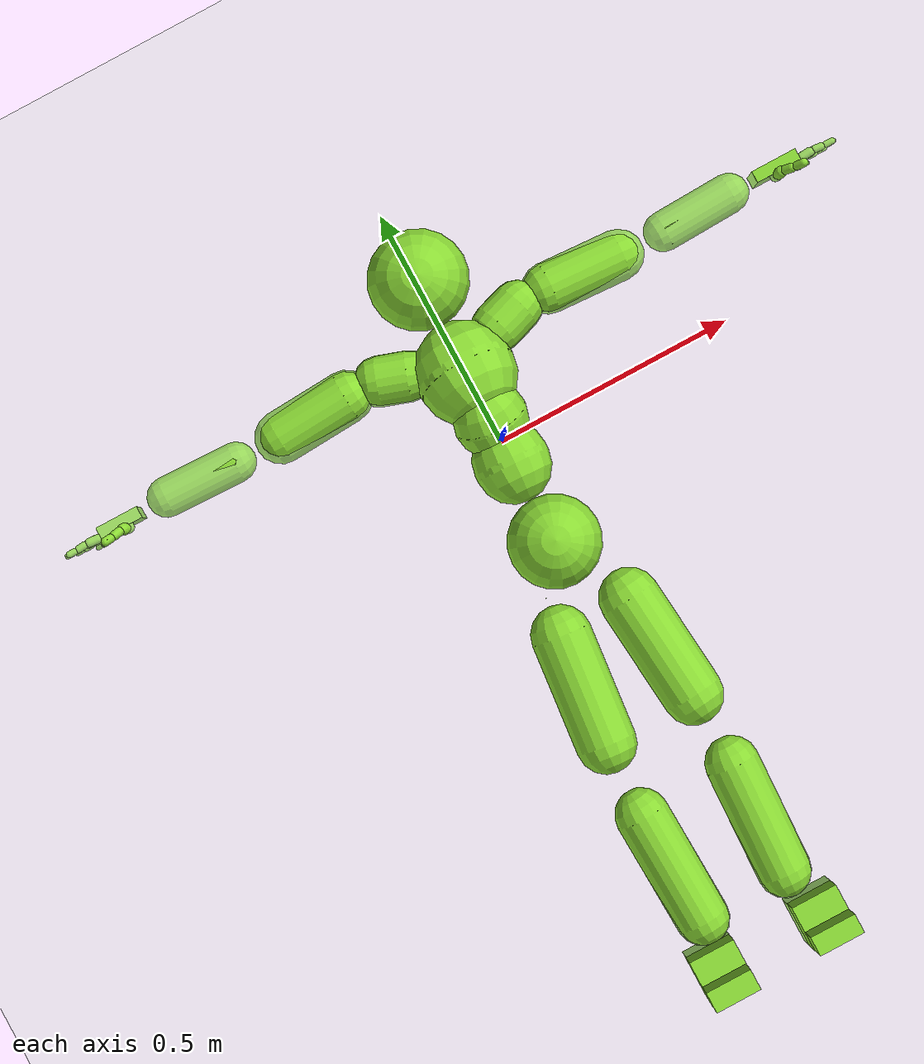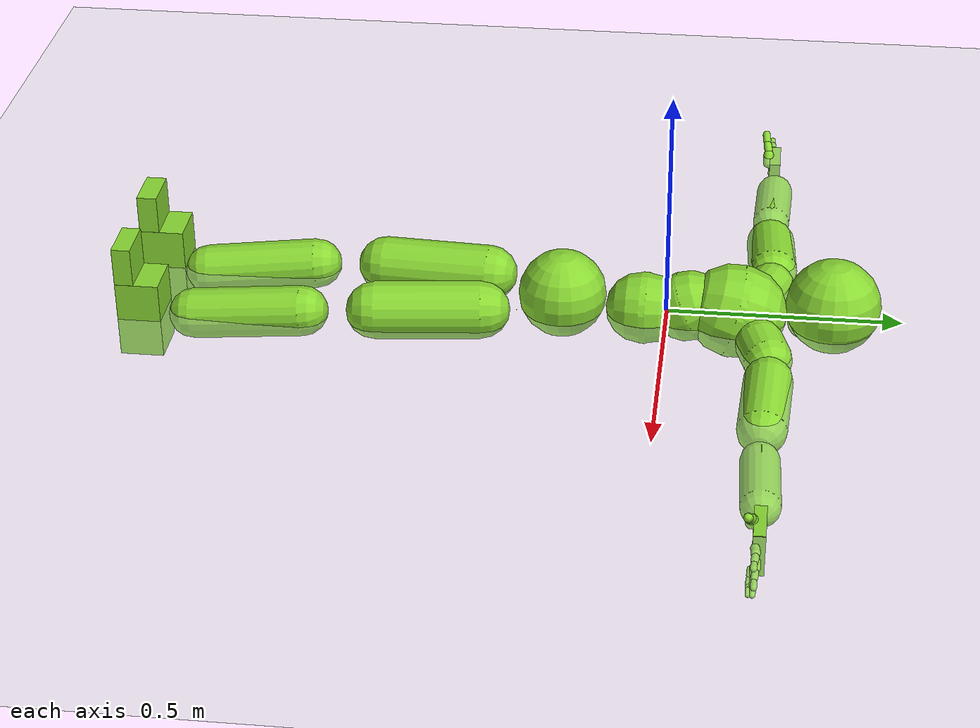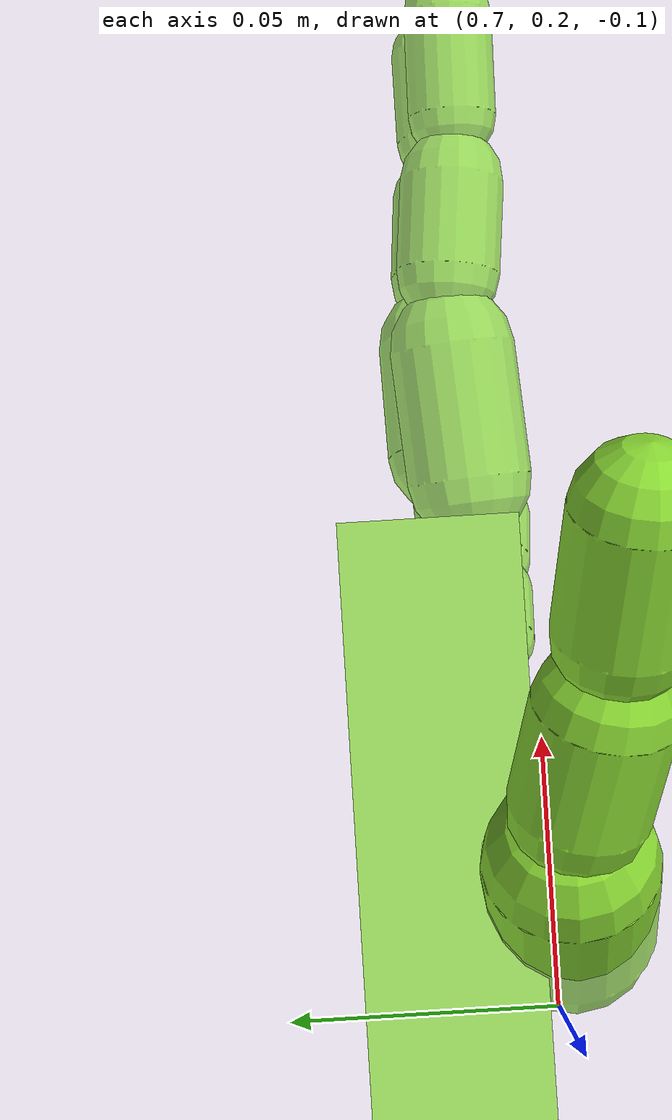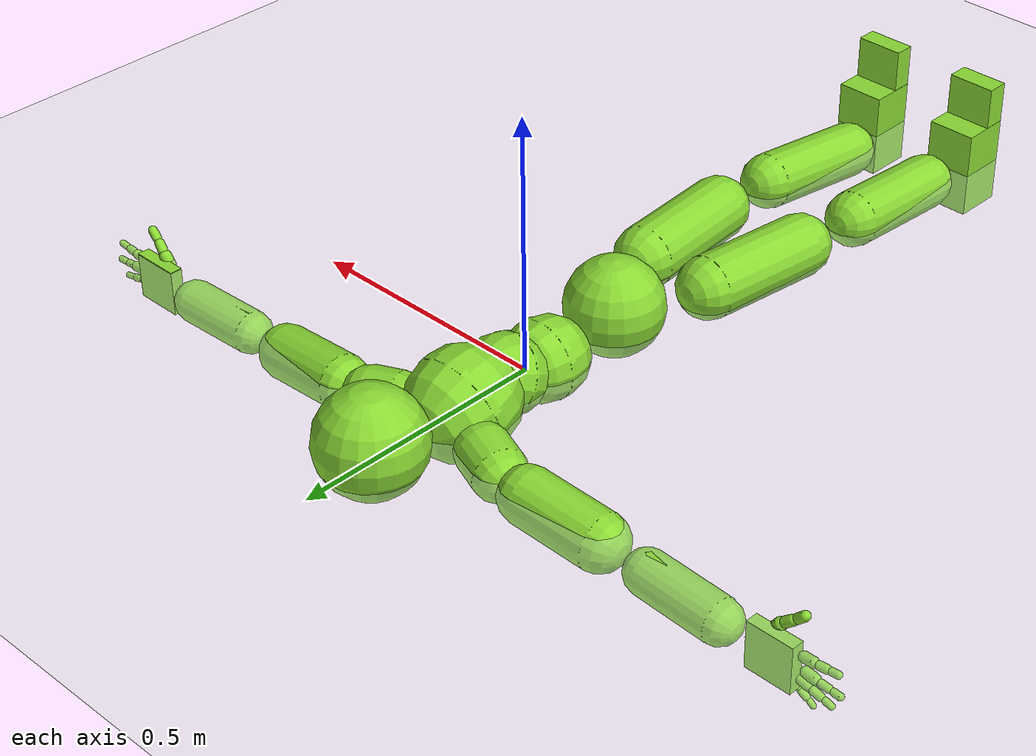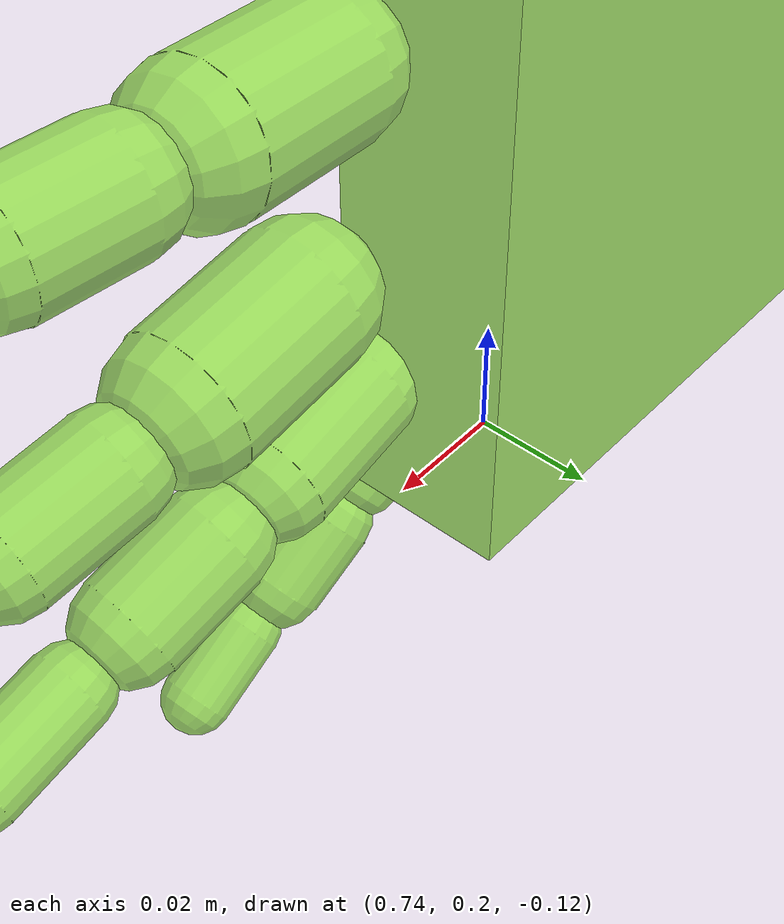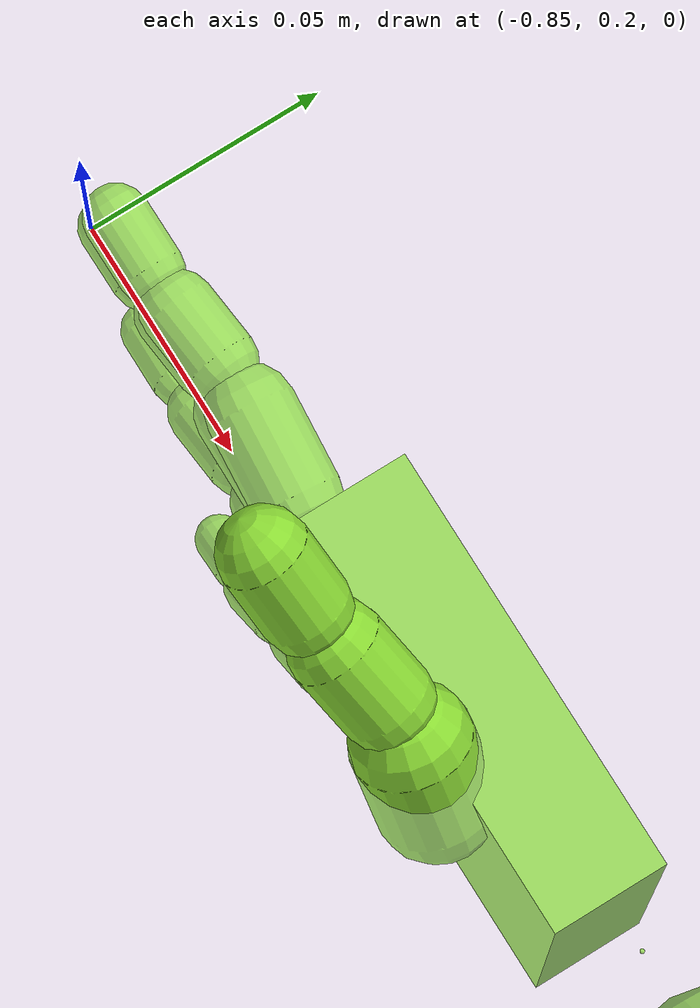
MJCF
<mujoco model="smplh_humanoid_xyz">
  <compiler coordinate="local" angle="radian" />
  <default>
    <joint damping="0.0" armature="0.01" stiffness="0.0" limited="true" />
    <geom conaffinity="1" condim="3" contype="7" margin="0.001" material="humanoid_green" />
  </default>
  <asset>
    <texture type="skybox" builtin="gradient" rgb1=".4 .5 .6" rgb2="0 0 0" width="100" height="100" />
    <texture builtin="flat" height="1278" mark="cross" markrgb="1 1 1" name="texgeom" random="0.01" rgb1="0.8 0.6 0.4" rgb2="0.8 0.6 0.4" type="cube" width="127" />
    <texture builtin="checker" height="100" name="texplane" rgb1="0 0 0" rgb2="0.8 0.8 0.8" type="2d" width="100" />
    <material name="MatPlane" reflectance="0.5" shininess="1" specular="1" texrepeat="60 60" texture="texplane" />
    <material name="humanoid_green" rgba="0.54 0.85 0.2 1" />
  </asset>
  <worldbody>
    <light cutoff="100" diffuse="1 1 1" dir="-0 0 -1.3" directional="true" exponent="1" pos="0 0 1.3" specular=".1 .1 .1" />
    <geom conaffinity="1" condim="3" name="floor" pos="0 0 0" rgba="0.8 0.9 0.8 1" size="100 100 .2" type="plane" material="MatPlane" />
    <body name="Pelvis" pos="-0.0018 -0.2233 0.0282">
      <joint name="floating_base_joint" type="free" />
      <geom type="sphere" contype="1" conaffinity="1" density="4629.6296296296305" size="0.0942" pos="0.0000 0.0000 0.0000" name="Pelvis" material="humanoid_green" />
      <body name="L_Hip_x" pos="0.0695 -0.0914 -0.0068">
        <joint name="L_Hip_x" type="hinge" pos="0 0 0" axis="1 0 0" user="250 2.5 1 500 10 2" armature="0.01" range="-0.01 0.01" damping="0" stiffness="0" />
        <geom type="sphere" contype="1" conaffinity="1" density="4629.6296296296305" size="0.0005" pos="0.0000 0.0000 0.0000" name="L_Hip_x" material="humanoid_green" />
        <body name="L_Hip_y" pos="0 0 0">
          <joint name="L_Hip_y" type="hinge" pos="0 0 0" axis="0 1 0" user="250 2.5 1 500 10 2" armature="0.01" range="-0.01 0.01" damping="0" stiffness="0" />
          <geom type="sphere" contype="1" conaffinity="1" density="4629.6296296296305" size="0.0005" pos="0.0000 0.0000 0.0000" name="L_Hip_y" material="humanoid_green" />
          <body name="L_Hip_z" pos="0 0 0">
            <joint name="L_Hip_z" type="hinge" pos="0 0 0" axis="0 0 1" user="250 2.5 1 500 10 2" armature="0.01" range="-0.01 0.01" damping="0" stiffness="0" />
            <geom type="capsule" contype="1" conaffinity="1" density="2040.816327" fromto="0.0069 -0.0750 -0.0009 0.0274 -0.3002 -0.0036" size="0.0615" name="L_Hip" material="humanoid_green" />
            <body name="L_Knee_x" pos="0.0343 -0.3752 -0.0045">
              <joint name="L_Knee_x" type="hinge" pos="0 0 0" axis="1 0 0" user="250 2.5 1 500 10 2" armature="0.01" range="-0.01 0.01" damping="0" stiffness="0" />
              <geom type="sphere" contype="1" conaffinity="1" density="4629.6296296296305" size="0.0005" pos="0.0000 0.0000 0.0000" name="L_Knee_x" material="humanoid_green" />
              <body name="L_Knee_y" pos="0 0 0">
                <joint name="L_Knee_y" type="hinge" pos="0 0 0" axis="0 1 0" user="250 2.5 1 500 10 2" armature="0.01" range="-0.01 0.01" damping="0" stiffness="0" />
                <geom type="sphere" contype="1" conaffinity="1" density="4629.6296296296305" size="0.0005" pos="0.0000 0.0000 0.0000" name="L_Knee_y" material="humanoid_green" />
                <body name="L_Knee_z" pos="0 0 0">
                  <joint name="L_Knee_z" type="hinge" pos="0 0 0" axis="0 0 1" user="250 2.5 1 500 10 2" armature="0.01" range="-0.01 0.01" damping="0" stiffness="0" />
                  <geom type="capsule" contype="1" conaffinity="1" density="1234.567901" fromto="-0.0027 -0.0796 -0.0087 -0.0109 -0.3184 -0.0350" size="0.0541" name="L_Knee" material="humanoid_green" />
                  <body name="L_Ankle_x" pos="-0.0136 -0.398 -0.0437">
                    <joint name="L_Ankle_x" type="hinge" pos="0 0 0" axis="1 0 0" user="150 2.5 1 500 10 2" armature="0.01" range="-0.01 0.01" damping="0" stiffness="0" />
                    <geom type="sphere" contype="1" conaffinity="1" density="4629.6296296296305" size="0.0005" pos="0.0000 0.0000 0.0000" name="L_Ankle_x" material="humanoid_green" />
                    <body name="L_Ankle_y" pos="0 0 0">
                      <joint name="L_Ankle_y" type="hinge" pos="0 0 0" axis="0 1 0" user="150 2.5 1 500 10 2" armature="0.01" range="-0.01 0.01" damping="0" stiffness="0" />
                      <geom type="sphere" contype="1" conaffinity="1" density="4629.6296296296305" size="0.0005" pos="0.0000 0.0000 0.0000" name="L_Ankle_y" material="humanoid_green" />
                      <body name="L_Ankle_z" pos="0 0 0">
                        <joint name="L_Ankle_z" type="hinge" pos="0 0 0" axis="0 0 1" user="150 2.5 1 500 10 2" armature="0.01" range="-0.01 0.01" damping="0" stiffness="0" />
                        <geom type="box" density="449.071564" pos="0.0233 -0.0239 0.0242" size="0.0483 0.0464 0.085" quat="1.0000 0.0000 0.0000 0.0000" name="L_Ankle" material="humanoid_green" />
                        <body name="L_Toe_x" pos="0.0264 -0.0558 0.1193">
                          <joint name="L_Toe_x" type="hinge" pos="0 0 0" axis="1 0 0" user="150 1 1 500 1 1" armature="0.01" range="-0.01 0.01" damping="0" stiffness="0" />
                          <geom type="sphere" contype="1" conaffinity="1" density="4629.6296296296305" size="0.0005" pos="0.0000 0.0000 0.0000" name="L_Toe_x" material="humanoid_green" />
                          <body name="L_Toe_y" pos="0 0 0">
                            <joint name="L_Toe_y" type="hinge" pos="0 0 0" axis="0 1 0" user="150 1 1 500 1 1" armature="0.01" range="-0.01 0.01" damping="0" stiffness="0" />
                            <geom type="sphere" contype="1" conaffinity="1" density="4629.6296296296305" size="0.0005" pos="0.0000 0.0000 0.0000" name="L_Toe_y" material="humanoid_green" />
                            <body name="L_Toe_z" pos="0 0 0">
                              <joint name="L_Toe_z" type="hinge" pos="0 0 0" axis="0 0 1" user="150 1 1 500 1 1" armature="0.01" range="-0.01 0.01" damping="0" stiffness="0" />
                              <geom type="box" density="423.206892" pos="-0.0030 0.0055 0.0248" size="0.0478 0.02 0.0496" quat="1.0000 0.0000 0.0000 0.0000" name="L_Toe" material="humanoid_green" />
                            </body>
                          </body>
                        </body>
                      </body>
                    </body>
                  </body>
                </body>
              </body>
            </body>
          </body>
        </body>
      </body>
      <body name="R_Hip_x" pos="-0.0677 -0.0905 -0.0043">
        <joint name="R_Hip_x" type="hinge" pos="0 0 0" axis="1 0 0" user="250 2.5 1 500 10 2" armature="0.01" range="-0.01 0.01" damping="0" stiffness="0" />
        <geom type="sphere" contype="1" conaffinity="1" density="4629.6296296296305" size="0.0005" pos="0.0000 0.0000 0.0000" name="R_Hip_x" material="humanoid_green" />
        <body name="R_Hip_y" pos="0 0 0">
          <joint name="R_Hip_y" type="hinge" pos="0 0 0" axis="0 1 0" user="250 2.5 1 500 10 2" armature="0.01" range="-0.01 0.01" damping="0" stiffness="0" />
          <geom type="sphere" contype="1" conaffinity="1" density="4629.6296296296305" size="0.0005" pos="0.0000 0.0000 0.0000" name="R_Hip_y" material="humanoid_green" />
          <body name="R_Hip_z" pos="0 0 0">
            <joint name="R_Hip_z" type="hinge" pos="0 0 0" axis="0 0 1" user="250 2.5 1 500 10 2" armature="0.01" range="-0.01 0.01" damping="0" stiffness="0" />
            <geom type="capsule" contype="1" conaffinity="1" density="2040.816327" fromto="-0.0077 -0.0765 -0.0018 -0.0306 -0.3061 -0.0071" size="0.0606" name="R_Hip" material="humanoid_green" />
            <body name="R_Knee_x" pos="-0.0383 -0.3826 -0.0089">
              <joint name="R_Knee_x" type="hinge" pos="0 0 0" axis="1 0 0" user="250 2.5 1 500 10 2" armature="0.01" range="-0.01 0.01" damping="0" stiffness="0" />
              <geom type="sphere" contype="1" conaffinity="1" density="4629.6296296296305" size="0.0005" pos="0.0000 0.0000 0.0000" name="R_Knee_x" material="humanoid_green" />
              <body name="R_Knee_y" pos="0 0 0">
                <joint name="R_Knee_y" type="hinge" pos="0 0 0" axis="0 1 0" user="250 2.5 1 500 10 2" armature="0.01" range="-0.01 0.01" damping="0" stiffness="0" />
                <geom type="sphere" contype="1" conaffinity="1" density="4629.6296296296305" size="0.0005" pos="0.0000 0.0000 0.0000" name="R_Knee_y" material="humanoid_green" />
                <body name="R_Knee_z" pos="0 0 0">
                  <joint name="R_Knee_z" type="hinge" pos="0 0 0" axis="0 0 1" user="250 2.5 1 500 10 2" armature="0.01" range="-0.01 0.01" damping="0" stiffness="0" />
                  <geom type="capsule" contype="1" conaffinity="1" density="1234.567901" fromto="0.0032 -0.0797 -0.0085 0.0126 -0.3187 -0.0338" size="0.0541" name="R_Knee" material="humanoid_green" />
                  <body name="R_Ankle_x" pos="0.0158 -0.3984 -0.0423">
                    <joint name="R_Ankle_x" type="hinge" pos="0 0 0" axis="1 0 0" user="150 1 1 500 10 2" armature="0.01" range="-0.01 0.01" damping="0" stiffness="0" />
                    <geom type="sphere" contype="1" conaffinity="1" density="4629.6296296296305" size="0.0005" pos="0.0000 0.0000 0.0000" name="R_Ankle_x" material="humanoid_green" />
                    <body name="R_Ankle_y" pos="0 0 0">
                      <joint name="R_Ankle_y" type="hinge" pos="0 0 0" axis="0 1 0" user="150 1 1 500 10 2" armature="0.01" range="-0.01 0.01" damping="0" stiffness="0" />
                      <geom type="sphere" contype="1" conaffinity="1" density="4629.6296296296305" size="0.0005" pos="0.0000 0.0000 0.0000" name="R_Ankle_y" material="humanoid_green" />
                      <body name="R_Ankle_z" pos="0 0 0">
                        <joint name="R_Ankle_z" type="hinge" pos="0 0 0" axis="0 0 1" user="150 1 1 500 10 2" armature="0.01" range="-0.01 0.01" damping="0" stiffness="0" />
                        <geom type="box" density="434.700981" pos="-0.0212 -0.0174 0.0256" size="0.0483 0.0478 0.0865" quat="1.0000 0.0000 0.0000 0.0000" name="R_Ankle" material="humanoid_green" />
                        <body name="R_Toe_x" pos="-0.0254 -0.0481 0.1233">
                          <joint name="R_Toe_x" type="hinge" pos="0 0 0" axis="1 0 0" user="150 1 1 500 1 1" armature="0.01" range="-0.01 0.01" damping="0" stiffness="0" />
                          <geom type="sphere" contype="1" conaffinity="1" density="4629.6296296296305" size="0.0005" pos="0.0000 0.0000 0.0000" name="R_Toe_x" material="humanoid_green" />
                          <body name="R_Toe_y" pos="0 0 0">
                            <joint name="R_Toe_y" type="hinge" pos="0 0 0" axis="0 1 0" user="150 1 1 500 1 1" armature="0.01" range="-0.01 0.01" damping="0" stiffness="0" />
                            <geom type="sphere" contype="1" conaffinity="1" density="4629.6296296296305" size="0.0005" pos="0.0000 0.0000 0.0000" name="R_Toe_y" material="humanoid_green" />
                            <body name="R_Toe_z" pos="0 0 0">
                              <joint name="R_Toe_z" type="hinge" pos="0 0 0" axis="0 0 1" user="150 1 1 500 1 1" armature="0.01" range="-0.01 0.01" damping="0" stiffness="0" />
                              <geom type="box" density="407.384095" pos="0.0042 0.0045 0.0227" size="0.0479 0.0216 0.0493" quat="1.0000 0.0000 0.0000 0.0000" name="R_Toe" material="humanoid_green" />
                            </body>
                          </body>
                        </body>
                      </body>
                    </body>
                  </body>
                </body>
              </body>
            </body>
          </body>
        </body>
      </body>
      <body name="Torso_x" pos="-0.0025 0.109 -0.0267">
        <joint name="Torso_x" type="hinge" pos="0 0 0" axis="1 0 0" user="500 5 1 500 10 2" armature="0.01" range="-1.0472 1.0472" damping="0" stiffness="0" />
        <geom type="sphere" contype="1" conaffinity="1" density="4629.6296296296305" size="0.0005" pos="0.0000 0.0000 0.0000" name="Torso_x" material="humanoid_green" />
        <body name="Torso_y" pos="0 0 0">
          <joint name="Torso_y" type="hinge" pos="0 0 0" axis="0 1 0" user="500 5 1 500 10 2" armature="0.01" range="-1.0472 1.0472" damping="0" stiffness="0" />
          <geom type="sphere" contype="1" conaffinity="1" density="4629.6296296296305" size="0.0005" pos="0.0000 0.0000 0.0000" name="Torso_y" material="humanoid_green" />
          <body name="Torso_z" pos="0 0 0">
            <joint name="Torso_z" type="hinge" pos="0 0 0" axis="0 0 1" user="500 5 1 500 10 2" armature="0.01" range="-1.0472 1.0472" damping="0" stiffness="0" />
            <geom type="capsule" contype="1" conaffinity="1" density="2040.816327" fromto="0.0025 0.0608 0.0005 0.0030 0.0743 0.0006" size="0.0769" name="Torso" material="humanoid_green" />
            <body name="Spine_x" pos="0.0055 0.1352 0.0011">
              <joint name="Spine_x" type="hinge" pos="0 0 0" axis="1 0 0" user="500 5 1 500 10 2" armature="0.01" range="-1.0472 1.0472" damping="0" stiffness="0" />
              <geom type="sphere" contype="1" conaffinity="1" density="4629.6296296296305" size="0.0005" pos="0.0000 0.0000 0.0000" name="Spine_x" material="humanoid_green" />
              <body name="Spine_y" pos="0 0 0">
                <joint name="Spine_y" type="hinge" pos="0 0 0" axis="0 1 0" user="500 5 1 500 10 2" armature="0.01" range="-1.0472 1.0472" damping="0" stiffness="0" />
                <geom type="sphere" contype="1" conaffinity="1" density="4629.6296296296305" size="0.0005" pos="0.0000 0.0000 0.0000" name="Spine_y" material="humanoid_green" />
                <body name="Spine_z" pos="0 0 0">
                  <joint name="Spine_z" type="hinge" pos="0 0 0" axis="0 0 1" user="500 5 1 500 10 2" armature="0.01" range="-1.0472 1.0472" damping="0" stiffness="0" />
                  <geom type="capsule" contype="1" conaffinity="1" density="2040.816327" fromto="0.0007 0.0238 0.0114 0.0008 0.0291 0.0140" size="0.0755" name="Spine" material="humanoid_green" />
                  <body name="Chest_x" pos="0.0015 0.0529 0.0254">
                    <joint name="Chest_x" type="hinge" pos="0 0 0" axis="1 0 0" user="500 5 1 500 10 2" armature="0.01" range="-1.0472 1.0472" damping="0" stiffness="0" />
                    <geom type="sphere" contype="1" conaffinity="1" density="4629.6296296296305" size="0.0005" pos="0.0000 0.0000 0.0000" name="Chest_x" material="humanoid_green" />
                    <body name="Chest_y" pos="0 0 0">
                      <joint name="Chest_y" type="hinge" pos="0 0 0" axis="0 1 0" user="500 5 1 500 10 2" armature="0.01" range="-1.0472 1.0472" damping="0" stiffness="0" />
                      <geom type="sphere" contype="1" conaffinity="1" density="4629.6296296296305" size="0.0005" pos="0.0000 0.0000 0.0000" name="Chest_y" material="humanoid_green" />
                      <body name="Chest_z" pos="0 0 0">
                        <joint name="Chest_z" type="hinge" pos="0 0 0" axis="0 0 1" user="500 5 1 500 10 2" armature="0.01" range="-1.0472 1.0472" damping="0" stiffness="0" />
                        <geom type="capsule" contype="1" conaffinity="1" density="2040.816327" fromto="-0.0009 0.0682 -0.0173 -0.0010 0.0833 -0.0212" size="0.1002" name="Chest"
                          material="humanoid_green" />
                        <body name="Neck_x" pos="-0.0028 0.2139 -0.0429">
                          <joint name="Neck_x" type="hinge" pos="0 0 0" axis="1 0 0" user="150 1 1 250 50 4" armature="0.01" range="-3.1416 3.1416" damping="0" stiffness="0" />
                          <geom type="sphere" contype="1" conaffinity="1" density="4629.6296296296305" size="0.0005" pos="0.0000 0.0000 0.0000" name="Neck_x" material="humanoid_green" />
                          <body name="Neck_y" pos="0 0 0">
                            <joint name="Neck_y" type="hinge" pos="0 0 0" axis="0 1 0" user="150 1 1 250 50 4" armature="0.01" range="-3.1416 3.1416" damping="0" stiffness="0" />
                            <geom type="sphere" contype="1" conaffinity="1" density="4629.6296296296305" size="0.0005" pos="0.0000 0.0000 0.0000" name="Neck_y" material="humanoid_green" />
                            <body name="Neck_z" pos="0 0 0">
                              <joint name="Neck_z" type="hinge" pos="0 0 0" axis="0 0 1" user="150 1 1 250 50 4" armature="0.01" range="-3.1416 3.1416" damping="0" stiffness="0" />
                              <geom type="capsule" contype="1" conaffinity="1" density="1000" fromto="0.0010 0.0130 0.0103 0.0041 0.0520 0.0411" size="0.0436" name="Neck" material="humanoid_green" />
                              <body name="Head_x" pos="0.0052 0.065 0.0513">
                                <joint name="Head_x" type="hinge" pos="0 0 0" axis="1 0 0" user="150 1 1 250 50 4" armature="0.01" range="-1.5708 1.5708" damping="0" stiffness="0" />
                                <geom type="sphere" contype="1" conaffinity="1" density="4629.6296296296305" size="0.0005" pos="0.0000 0.0000 0.0000" name="Head_x" material="humanoid_green" />
                                <body name="Head_y" pos="0 0 0">
                                  <joint name="Head_y" type="hinge" pos="0 0 0" axis="0 1 0" user="150 1 1 250 50 4" armature="0.01" range="-1.5708 1.5708" damping="0" stiffness="0" />
                                  <geom type="sphere" contype="1" conaffinity="1" density="4629.6296296296305" size="0.0005" pos="0.0000 0.0000 0.0000" name="Head_y" material="humanoid_green" />
                                  <body name="Head_z" pos="0 0 0">
                                    <joint name="Head_z" type="hinge" pos="0 0 0" axis="0 0 1" user="150 1 1 250 50 4" armature="0.01" range="-1.5708 1.5708" damping="0" stiffness="0" />
                                    <geom type="sphere" contype="1" conaffinity="1" density="1000" size="0.1011" pos="0.0000 0.0000 0.0000" name="Head" material="humanoid_green" />
                                  </body>
                                </body>
                              </body>
                            </body>
                          </body>
                        </body>
                        <body name="L_Thorax_x" pos="0.0788 0.1217 -0.0341">
                          <joint name="L_Thorax_x" type="hinge" pos="0 0 0" axis="1 0 0" user="200 2 1 500 50 4" armature="0.01" range="-3.1416 3.1416" damping="0" stiffness="0" />
                          <geom type="sphere" contype="1" conaffinity="1" density="4629.6296296296305" size="0.0005" pos="0.0000 0.0000 0.0000" name="L_Thorax_x" material="humanoid_green" />
                          <body name="L_Thorax_y" pos="0 0 0">
                            <joint name="L_Thorax_y" type="hinge" pos="0 0 0" axis="0 1 0" user="200 2 1 500 50 4" armature="0.01" range="-3.1416 3.1416" damping="0" stiffness="0" />
                            <geom type="sphere" contype="1" conaffinity="1" density="4629.6296296296305" size="0.0005" pos="0.0000 0.0000 0.0000" name="L_Thorax_y" material="humanoid_green" />
                            <body name="L_Thorax_z" pos="0 0 0">
                              <joint name="L_Thorax_z" type="hinge" pos="0 0 0" axis="0 0 1" user="200 2 1 500 50 4" armature="0.01" range="-3.1416 3.1416" damping="0" stiffness="0" />
                              <geom type="capsule" contype="1" conaffinity="1" density="1000" fromto="0.0182 0.0061 -0.0018 0.0728 0.0244 -0.0071" size="0.0521" name="L_Thorax"
                                material="humanoid_green" />
                              <body name="L_Shoulder_x" pos="0.091 0.0305 -0.0089">
                                <joint name="L_Shoulder_x" type="hinge" pos="0 0 0" axis="1 0 0" user="200 2 1 500 50 4" armature="0.01" range="-3.1416 3.1416" damping="0" stiffness="0" />
                                <geom type="sphere" contype="1" conaffinity="1" density="4629.6296296296305" size="0.0005" pos="0.0000 0.0000 0.0000" name="L_Shoulder_x" material="humanoid_green" />
                                <body name="L_Shoulder_y" pos="0 0 0">
                                  <joint name="L_Shoulder_y" type="hinge" pos="0 0 0" axis="0 1 0" user="200 2 1 500 50 4" armature="0.01" range="-3.1416 3.1416" damping="0" stiffness="0" />
                                  <geom type="sphere" contype="1" conaffinity="1" density="4629.6296296296305" size="0.0005" pos="0.0000 0.0000 0.0000" name="L_Shoulder_y" material="humanoid_green" />
                                  <body name="L_Shoulder_z" pos="0 0 0">
                                    <joint name="L_Shoulder_z" type="hinge" pos="0 0 0" axis="0 0 1" user="200 2 1 500 50 4" armature="0.01" range="-3.1416 3.1416" damping="0" stiffness="0" />
                                    <geom type="capsule" contype="1" conaffinity="1" density="1000" fromto="0.0519 -0.0026 -0.0055 0.2077 -0.0102 -0.0220" size="0.0517" name="L_Shoulder"
                                      material="humanoid_green" />
                                    <body name="L_Elbow_x" pos="0.2596 -0.0128 -0.0275">
                                      <joint name="L_Elbow_x" type="hinge" pos="0 0 0" axis="1 0 0" user="150 1 1 150 10 2" armature="0.01" range="-12.5664 12.5664" damping="0" stiffness="0" />
                                      <geom type="sphere" contype="1" conaffinity="1" density="4629.6296296296305" size="0.0005" pos="0.0000 0.0000 0.0000" name="L_Elbow_x" material="humanoid_green" />
                                      <body name="L_Elbow_y" pos="0 0 0">
                                        <joint name="L_Elbow_y" type="hinge" pos="0 0 0" axis="0 1 0" user="150 1 1 150 10 2" armature="0.01" range="-12.5664 12.5664" damping="0" stiffness="0" />
                                        <geom type="sphere" contype="1" conaffinity="1" density="4629.6296296296305" size="0.0005" pos="0.0000 0.0000 0.0000" name="L_Elbow_y" material="humanoid_green" />
                                        <body name="L_Elbow_z" pos="0 0 0">
                                          <joint name="L_Elbow_z" type="hinge" pos="0 0 0" axis="0 0 1" user="150 1 1 150 10 2" armature="0.01" range="-12.5664 12.5664" damping="0" stiffness="0" />
                                          <geom type="capsule" contype="1" conaffinity="1" density="1000" fromto="0.0498 0.0018 -0.0002 0.1994 0.0072 -0.0009" size="0.0405" name="L_Elbow"
                                            material="humanoid_green" />
                                          <body name="L_Wrist_x" pos="0.2492 0.009 -0.0012">
                                            <joint name="L_Wrist_x" type="hinge" pos="0 0 0" axis="1 0 0" user="100 1 1 150 1 1" armature="0.01" range="-3.1416 3.1416" damping="0" stiffness="0" />
                                            <geom type="sphere" contype="1" conaffinity="1" density="4629.6296296296305" size="0.0005" pos="0.0000 0.0000 0.0000" name="L_Wrist_x"
                                              material="humanoid_green" />
                                            <body name="L_Wrist_y" pos="0 0 0">
                                              <joint name="L_Wrist_y" type="hinge" pos="0 0 0" axis="0 1 0" user="100 1 1 150 1 1" armature="0.01" range="-3.1416 3.1416" damping="0" stiffness="0" />
                                              <geom type="sphere" contype="1" conaffinity="1" density="4629.6296296296305" size="0.0005" pos="0.0000 0.0000 0.0000" name="L_Wrist_y"
                                                material="humanoid_green" />
                                              <body name="L_Wrist_z" pos="0 0 0">
                                                <joint name="L_Wrist_z" type="hinge" pos="0 0 0" axis="0 0 1" user="100 1 1 150 1 1" armature="0.01" range="-3.1416 3.1416" damping="0" stiffness="0" />
                                                <geom type="box" density="1198.335963" pos="0.0523 -0.0013 -0.0031" size="0.0484 0.0122 0.046" quat="1.0000 0.0000 0.0000 0.0000" name="L_Wrist"
                                                  material="humanoid_green" />
                                                <body name="L_Index1_x" pos="0.1019 -0.0087 0.0194">
                                                  <joint name="L_Index1_x" type="hinge" pos="0 0 0" axis="1 0 0" stiffness="0" damping="0" armature="0.01" range="-3.1416 3.1416" />
                                                  <geom type="sphere" contype="1" conaffinity="1" density="4629.6296296296305" size="0.0005" pos="0.0000 0.0000 0.0000" name="L_Index1_x"
                                                    material="humanoid_green" />
                                                  <body name="L_Index1_y" pos="0 0 0">
                                                    <joint name="L_Index1_y" type="hinge" pos="0 0 0" axis="0 1 0" stiffness="0" damping="0" armature="0.01" range="-3.1416 3.1416" />
                                                    <geom type="sphere" contype="1" conaffinity="1" density="4629.6296296296305" size="0.0005" pos="0.0000 0.0000 0.0000" name="L_Index1_y"
                                                      material="humanoid_green" />
                                                    <body name="L_Index1_z" pos="0 0 0">
                                                      <joint name="L_Index1_z" type="hinge" pos="0 0 0" axis="0 0 1" stiffness="0" damping="0" armature="0.01" range="-3.1416 3.1416" />
                                                      <geom type="capsule" contype="1" conaffinity="1" density="1000" fromto="0.0064 0.0004 0.0006 0.0256 0.0018 0.0024" size="0.0091" name="L_Index1"
                                                        material="humanoid_green" />
                                                      <body name="L_Index2_x" pos="0.0319 0.0022 0.003">
                                                        <joint name="L_Index2_x" type="hinge" pos="0 0 0" axis="1 0 0" stiffness="0" damping="0" armature="0.01" range="-3.1416 3.1416" />
                                                        <geom type="sphere" contype="1" conaffinity="1" density="4629.6296296296305" size="0.0005" pos="0.0000 0.0000 0.0000" name="L_Index2_x"
                                                          material="humanoid_green" />
                                                        <body name="L_Index2_y" pos="0 0 0">
                                                          <joint name="L_Index2_y" type="hinge" pos="0 0 0" axis="0 1 0" stiffness="0" damping="0" armature="0.01" range="-3.1416 3.1416" />
                                                          <geom type="sphere" contype="1" conaffinity="1" density="4629.6296296296305" size="0.0005" pos="0.0000 0.0000 0.0000" name="L_Index2_y"
                                                            material="humanoid_green" />
                                                          <body name="L_Index2_z" pos="0 0 0">
                                                            <joint name="L_Index2_z" type="hinge" pos="0 0 0" axis="0 0 1" stiffness="0" damping="0" armature="0.01" range="-3.1416 3.1416" />
                                                            <geom type="capsule" contype="1" conaffinity="1" density="1000" fromto="0.0045 -0.0005 0.0000 0.0180 -0.0019 0.0000" size="0.0076"
                                                              name="L_Index2" material="humanoid_green" />
                                                            <body name="L_Index3_x" pos="0.0225 -0.0024 0.0001">
                                                              <joint name="L_Index3_x" type="hinge" pos="0 0 0" axis="1 0 0" stiffness="0" damping="0" armature="0.01" range="-3.1416 3.1416" />
                                                              <geom type="sphere" contype="1" conaffinity="1" density="4629.6296296296305" size="0.0005" pos="0.0000 0.0000 0.0000" name="L_Index3_x"
                                                                material="humanoid_green" />
                                                              <body name="L_Index3_y" pos="0 0 0">
                                                                <joint name="L_Index3_y" type="hinge" pos="0 0 0" axis="0 1 0" stiffness="0" damping="0" armature="0.01" range="-3.1416 3.1416" />
                                                                <geom type="sphere" contype="1" conaffinity="1" density="4629.6296296296305" size="0.0005" pos="0.0000 0.0000 0.0000" name="L_Index3_y"
                                                                  material="humanoid_green" />
                                                                <body name="L_Index3_z" pos="0 0 0">
                                                                  <joint name="L_Index3_z" type="hinge" pos="0 0 0" axis="0 0 1" stiffness="0" damping="0" armature="0.01" range="-3.1416 3.1416" />
                                                                  <geom type="capsule" contype="1" conaffinity="1" density="1000" fromto="0.0049 -0.0001 0.0004 0.0196 -0.0003 0.0016" size="0.0064"
                                                                    name="L_Index3" material="humanoid_green" />
                                                                </body>
                                                              </body>
                                                            </body>
                                                          </body>
                                                        </body>
                                                      </body>
                                                    </body>
                                                  </body>
                                                </body>
                                                <body name="L_Middle1_x" pos="0.1094 -0.0063 -0.004">
                                                  <joint name="L_Middle1_x" type="hinge" pos="0 0 0" axis="1 0 0" stiffness="0" damping="0" armature="0.01" range="-3.1416 3.1416" />
                                                  <geom type="sphere" contype="1" conaffinity="1" density="4629.6296296296305" size="0.0005" pos="0.0000 0.0000 0.0000" name="L_Middle1_x"
                                                    material="humanoid_green" />
                                                  <body name="L_Middle1_y" pos="0 0 0">
                                                    <joint name="L_Middle1_y" type="hinge" pos="0 0 0" axis="0 1 0" stiffness="0" damping="0" armature="0.01" range="-3.1416 3.1416" />
                                                    <geom type="sphere" contype="1" conaffinity="1" density="4629.6296296296305" size="0.0005" pos="0.0000 0.0000 0.0000" name="L_Middle1_y"
                                                      material="humanoid_green" />
                                                    <body name="L_Middle1_z" pos="0 0 0">
                                                      <joint name="L_Middle1_z" type="hinge" pos="0 0 0" axis="0 0 1" stiffness="0" damping="0" armature="0.01" range="-3.1416 3.1416" />
                                                      <geom type="capsule" contype="1" conaffinity="1" density="1000" fromto="0.0061 0.0002 -0.0008 0.0245 0.0006 -0.0032" size="0.0094"
                                                        name="L_Middle1" material="humanoid_green" />
                                                      <body name="L_Middle2_x" pos="0.0306 0.0008 -0.004">
                                                        <joint name="L_Middle2_x" type="hinge" pos="0 0 0" axis="1 0 0" stiffness="0" damping="0" armature="0.01" range="-3.1416 3.1416" />
                                                        <geom type="sphere" contype="1" conaffinity="1" density="4629.6296296296305" size="0.0005" pos="0.0000 0.0000 0.0000" name="L_Middle2_x"
                                                          material="humanoid_green" />
                                                        <body name="L_Middle2_y" pos="0 0 0">
                                                          <joint name="L_Middle2_y" type="hinge" pos="0 0 0" axis="0 1 0" stiffness="0" damping="0" armature="0.01" range="-3.1416 3.1416" />
                                                          <geom type="sphere" contype="1" conaffinity="1" density="4629.6296296296305" size="0.0005" pos="0.0000 0.0000 0.0000" name="L_Middle2_y"
                                                            material="humanoid_green" />
                                                          <body name="L_Middle2_z" pos="0 0 0">
                                                            <joint name="L_Middle2_z" type="hinge" pos="0 0 0" axis="0 0 1" stiffness="0" damping="0" armature="0.01" range="-3.1416 3.1416" />
                                                            <geom type="capsule" contype="1" conaffinity="1" density="1000" fromto="0.0047 -0.0004 -0.0008 0.0188 -0.0016 -0.0033" size="0.007"
                                                              name="L_Middle2" material="humanoid_green" />
                                                            <body name="L_Middle3_x" pos="0.0235 -0.002 -0.0041">
                                                              <joint name="L_Middle3_x" type="hinge" pos="0 0 0" axis="1 0 0" stiffness="0" damping="0" armature="0.01" range="-3.1416 3.1416" />
                                                              <geom type="sphere" contype="1" conaffinity="1" density="4629.6296296296305" size="0.0005" pos="0.0000 0.0000 0.0000" name="L_Middle3_x"
                                                                material="humanoid_green" />
                                                              <body name="L_Middle3_y" pos="0 0 0">
                                                                <joint name="L_Middle3_y" type="hinge" pos="0 0 0" axis="0 1 0" stiffness="0" damping="0" armature="0.01" range="-3.1416 3.1416" />
                                                                <geom type="sphere" contype="1" conaffinity="1" density="4629.6296296296305" size="0.0005" pos="0.0000 0.0000 0.0000" name="L_Middle3_y"
                                                                  material="humanoid_green" />
                                                                <body name="L_Middle3_z" pos="0 0 0">
                                                                  <joint name="L_Middle3_z" type="hinge" pos="0 0 0" axis="0 0 1" stiffness="0" damping="0" armature="0.01" range="-3.1416 3.1416" />
                                                                  <geom type="capsule" contype="1" conaffinity="1" density="1000" fromto="0.0051 -0.0000 -0.0004 0.0204 -0.0000 -0.0017" size="0.0061"
                                                                    name="L_Middle3" material="humanoid_green" />
                                                                </body>
                                                              </body>
                                                            </body>
                                                          </body>
                                                        </body>
                                                      </body>
                                                    </body>
                                                  </body>
                                                </body>
                                                <body name="L_Pinky1_x" pos="0.084 -0.0145 -0.0437">
                                                  <joint name="L_Pinky1_x" type="hinge" pos="0 0 0" axis="1 0 0" stiffness="0" damping="0" armature="0.01" range="-3.1416 3.1416" />
                                                  <geom type="sphere" contype="1" conaffinity="1" density="4629.6296296296305" size="0.0005" pos="0.0000 0.0000 0.0000" name="L_Pinky1_x"
                                                    material="humanoid_green" />
                                                  <body name="L_Pinky1_y" pos="0 0 0">
                                                    <joint name="L_Pinky1_y" type="hinge" pos="0 0 0" axis="0 1 0" stiffness="0" damping="0" armature="0.01" range="-3.1416 3.1416" />
                                                    <geom type="sphere" contype="1" conaffinity="1" density="4629.6296296296305" size="0.0005" pos="0.0000 0.0000 0.0000" name="L_Pinky1_y"
                                                      material="humanoid_green" />
                                                    <body name="L_Pinky1_z" pos="0 0 0">
                                                      <joint name="L_Pinky1_z" type="hinge" pos="0 0 0" axis="0 0 1" stiffness="0" damping="0" armature="0.01" range="-3.1416 3.1416" />
                                                      <geom type="capsule" contype="1" conaffinity="1" density="1000" fromto="0.0031 -0.0002 -0.0024 0.0124 -0.0009 -0.0096" size="0.0067"
                                                        name="L_Pinky1" material="humanoid_green" />
                                                      <body name="L_Pinky2_x" pos="0.0155 -0.0011 -0.012">
                                                        <joint name="L_Pinky2_x" type="hinge" pos="0 0 0" axis="1 0 0" stiffness="0" damping="0" armature="0.01" range="-3.1416 3.1416" />
                                                        <geom type="sphere" contype="1" conaffinity="1" density="4629.6296296296305" size="0.0005" pos="0.0000 0.0000 0.0000" name="L_Pinky2_x"
                                                          material="humanoid_green" />
                                                        <body name="L_Pinky2_y" pos="0 0 0">
                                                          <joint name="L_Pinky2_y" type="hinge" pos="0 0 0" axis="0 1 0" stiffness="0" damping="0" armature="0.01" range="-3.1416 3.1416" />
                                                          <geom type="sphere" contype="1" conaffinity="1" density="4629.6296296296305" size="0.0005" pos="0.0000 0.0000 0.0000" name="L_Pinky2_y"
                                                            material="humanoid_green" />
                                                          <body name="L_Pinky2_z" pos="0 0 0">
                                                            <joint name="L_Pinky2_z" type="hinge" pos="0 0 0" axis="0 0 1" stiffness="0" damping="0" armature="0.01" range="-3.1416 3.1416" />
                                                            <geom type="capsule" contype="1" conaffinity="1" density="1000" fromto="0.0031 -0.0003 -0.0022 0.0124 -0.0013 -0.0090" size="0.0065"
                                                              name="L_Pinky2" material="humanoid_green" />
                                                            <body name="L_Pinky3_x" pos="0.0155 -0.0017 -0.0112">
                                                              <joint name="L_Pinky3_x" type="hinge" pos="0 0 0" axis="1 0 0" stiffness="0" damping="0" armature="0.01" range="-3.1416 3.1416" />
                                                              <geom type="sphere" contype="1" conaffinity="1" density="4629.6296296296305" size="0.0005" pos="0.0000 0.0000 0.0000" name="L_Pinky3_x"
                                                                material="humanoid_green" />
                                                              <body name="L_Pinky3_y" pos="0 0 0">
                                                                <joint name="L_Pinky3_y" type="hinge" pos="0 0 0" axis="0 1 0" stiffness="0" damping="0" armature="0.01" range="-3.1416 3.1416" />
                                                                <geom type="sphere" contype="1" conaffinity="1" density="4629.6296296296305" size="0.0005" pos="0.0000 0.0000 0.0000" name="L_Pinky3_y"
                                                                  material="humanoid_green" />
                                                                <body name="L_Pinky3_z" pos="0 0 0">
                                                                  <joint name="L_Pinky3_z" type="hinge" pos="0 0 0" axis="0 0 1" stiffness="0" damping="0" armature="0.01" range="-3.1416 3.1416" />
                                                                  <geom type="capsule" contype="1" conaffinity="1" density="1000" fromto="0.0035 0.0001 -0.0018 0.0140 0.0003 -0.0074" size="0.005"
                                                                    name="L_Pinky3" material="humanoid_green" />
                                                                </body>
                                                              </body>
                                                            </body>
                                                          </body>
                                                        </body>
                                                      </body>
                                                    </body>
                                                  </body>
                                                </body>
                                                <body name="L_Ring1" pos="0.0974 -0.0093 -0.0273">
                                                  <joint name="L_Ring1_x" type="hinge" pos="0 0 0" axis="1 0 0" stiffness="0" damping="0" armature="0.01" range="-3.1416 3.1416" />
                                                  <geom type="sphere" contype="1" conaffinity="1" density="4629.6296296296305" size="0.0005" pos="0.0000 0.0000 0.0000" name="L_Ring1_x"
                                                    material="humanoid_green" />
                                                  <body name="L_Ring1_y" pos="0 0 0">
                                                    <joint name="L_Ring1_y" type="hinge" pos="0 0 0" axis="0 1 0" stiffness="0" damping="0" armature="0.01" range="-3.1416 3.1416" />
                                                    <geom type="sphere" contype="1" conaffinity="1" density="4629.6296296296305" size="0.0005" pos="0.0000 0.0000 0.0000" name="L_Ring1_y"
                                                      material="humanoid_green" />
                                                    <body name="L_Ring1_z" pos="0 0 0">
                                                      <joint name="L_Ring1_z" type="hinge" pos="0 0 0" axis="0 0 1" stiffness="0" damping="0" armature="0.01" range="-3.1416 3.1416" />
                                                      <geom type="capsule" contype="1" conaffinity="1" density="1000" fromto="0.0056 0.0003 -0.0011 0.0224 0.0012 -0.0042" size="0.008" name="L_Ring1"
                                                        material="humanoid_green" />
                                                      <body name="L_Ring2_x" pos="0.028 0.0015 -0.0053">
                                                        <joint name="L_Ring2_x" type="hinge" pos="0 0 0" axis="1 0 0" stiffness="0" damping="0" armature="0.01" range="-3.1416 3.1416" />
                                                        <geom type="sphere" contype="1" conaffinity="1" density="4629.6296296296305" size="0.0005" pos="0.0000 0.0000 0.0000" name="L_Ring2_x"
                                                          material="humanoid_green" />
                                                        <body name="L_Ring2_y" pos="0 0 0">
                                                          <joint name="L_Ring2_y" type="hinge" pos="0 0 0" axis="0 1 0" stiffness="0" damping="0" armature="0.01" range="-3.1416 3.1416" />
                                                          <geom type="sphere" contype="1" conaffinity="1" density="4629.6296296296305" size="0.0005" pos="0.0000 0.0000 0.0000" name="L_Ring2_y"
                                                            material="humanoid_green" />
                                                          <body name="L_Ring2_z" pos="0 0 0">
                                                            <joint name="L_Ring2_z" type="hinge" pos="0 0 0" axis="0 0 1" stiffness="0" damping="0" armature="0.01" range="-3.1416 3.1416" />
                                                            <geom type="capsule" contype="1" conaffinity="1" density="1000" fromto="0.0046 -0.0003 -0.0014 0.0183 -0.0012 -0.0057" size="0.0074"
                                                              name="L_Ring2" material="humanoid_green" />
                                                            <body name="L_Ring3_x" pos="0.0228 -0.0015 -0.0071">
                                                              <joint name="L_Ring3_x" type="hinge" pos="0 0 0" axis="1 0 0" stiffness="0" damping="0" armature="0.01" range="-3.1416 3.1416" />
                                                              <geom type="sphere" contype="1" conaffinity="1" density="4629.6296296296305" size="0.0005" pos="0.0000 0.0000 0.0000" name="L_Ring3_x"
                                                                material="humanoid_green" />
                                                              <body name="L_Ring3_y" pos="0 0 0">
                                                                <joint name="L_Ring3_y" type="hinge" pos="0 0 0" axis="0 1 0" stiffness="0" damping="0" armature="0.01" range="-3.1416 3.1416" />
                                                                <geom type="sphere" contype="1" conaffinity="1" density="4629.6296296296305" size="0.0005" pos="0.0000 0.0000 0.0000" name="L_Ring3_y"
                                                                  material="humanoid_green" />
                                                                <body name="L_Ring3_z" pos="0 0 0">
                                                                  <joint name="L_Ring3_z" type="hinge" pos="0 0 0" axis="0 0 1" stiffness="0" damping="0" armature="0.01" range="-3.1416 3.1416" />
                                                                  <geom type="capsule" contype="1" conaffinity="1" density="1000" fromto="0.0050 0.0001 -0.0010 0.0199 0.0004 -0.0041" size="0.0057"
                                                                    name="L_Ring3" material="humanoid_green" />
                                                                </body>
                                                              </body>
                                                            </body>
                                                          </body>
                                                        </body>
                                                      </body>
                                                    </body>
                                                  </body>
                                                </body>
                                                <body name="L_Thumb1_x" pos="0.0406 -0.018 0.0256">
                                                  <joint name="L_Thumb1_x" type="hinge" pos="0 0 0" axis="1 0 0" stiffness="0" damping="0" armature="0.01" range="-3.1416 3.1416" />
                                                  <geom type="sphere" contype="1" conaffinity="1" density="4629.6296296296305" size="0.0005" pos="0.0000 0.0000 0.0000" name="L_Thumb1_x"
                                                    material="humanoid_green" />
                                                  <body name="L_Thumb1_y" pos="0 0 0">
                                                    <joint name="L_Thumb1_y" type="hinge" pos="0 0 0" axis="0 1 0" stiffness="0" damping="0" armature="0.01" range="-3.1416 3.1416" />
                                                    <geom type="sphere" contype="1" conaffinity="1" density="4629.6296296296305" size="0.0005" pos="0.0000 0.0000 0.0000" name="L_Thumb1_y"
                                                      material="humanoid_green" />
                                                    <body name="L_Thumb1_z" pos="0 0 0">
                                                      <joint name="L_Thumb1_z" type="hinge" pos="0 0 0" axis="0 0 1" stiffness="0" damping="0" armature="0.01" range="-3.1416 3.1416" />
                                                      <geom type="capsule" contype="1" conaffinity="1" density="1000" fromto="0.0034 0.0002 0.0050 0.0136 0.0008 0.0200" size="0.012" name="L_Thumb1"
                                                        material="humanoid_green" />
                                                      <body name="L_Thumb2_x" pos="0.017 0.001 0.025">
                                                        <joint name="L_Thumb2_x" type="hinge" pos="0 0 0" axis="1 0 0" stiffness="0" damping="0" armature="0.01" range="-3.1416 3.1416" />
                                                        <geom type="sphere" contype="1" conaffinity="1" density="4629.6296296296305" size="0.0005" pos="0.0000 0.0000 0.0000" name="L_Thumb2_x"
                                                          material="humanoid_green" />
                                                        <body name="L_Thumb2_y" pos="0 0 0">
                                                          <joint name="L_Thumb2_y" type="hinge" pos="0 0 0" axis="0 1 0" stiffness="0" damping="0" armature="0.01" range="-3.1416 3.1416" />
                                                          <geom type="sphere" contype="1" conaffinity="1" density="4629.6296296296305" size="0.0005" pos="0.0000 0.0000 0.0000" name="L_Thumb2_y"
                                                            material="humanoid_green" />
                                                          <body name="L_Thumb2_z" pos="0 0 0">
                                                            <joint name="L_Thumb2_z" type="hinge" pos="0 0 0" axis="0 0 1" stiffness="0" damping="0" armature="0.01" range="-3.1416 3.1416" />
                                                            <geom type="capsule" contype="1" conaffinity="1" density="1000" fromto="0.0041 -0.0010 0.0031 0.0164 -0.0041 0.0124" size="0.0095"
                                                              name="L_Thumb2" material="humanoid_green" />
                                                            <body name="L_Thumb3_x" pos="0.0205 -0.0052 0.0155">
                                                              <joint name="L_Thumb3_x" type="hinge" pos="0 0 0" axis="1 0 0" stiffness="0" damping="0" armature="0.01" range="-3.1416 3.1416" />
                                                              <geom type="sphere" contype="1" conaffinity="1" density="4629.6296296296305" size="0.0005" pos="0.0000 0.0000 0.0000" name="L_Thumb3_x"
                                                                material="humanoid_green" />
                                                              <body name="L_Thumb3_y" pos="0 0 0">
                                                                <joint name="L_Thumb3_y" type="hinge" pos="0 0 0" axis="0 1 0" stiffness="0" damping="0" armature="0.01" range="-3.1416 3.1416" />
                                                                <geom type="sphere" contype="1" conaffinity="1" density="4629.6296296296305" size="0.0005" pos="0.0000 0.0000 0.0000" name="L_Thumb3_y"
                                                                  material="humanoid_green" />
                                                                <body name="L_Thumb3_z" pos="0 0 0">
                                                                  <joint name="L_Thumb3_z" type="hinge" pos="0 0 0" axis="0 0 1" stiffness="0" damping="0" armature="0.01" range="-3.1416 3.1416" />
                                                                  <geom type="capsule" contype="1" conaffinity="1" density="1000" fromto="0.0045 -0.0006 0.0035 0.0180 -0.0025 0.0140" size="0.0087"
                                                                    name="L_Thumb3" material="humanoid_green" />
                                                                </body>
                                                              </body>
                                                            </body>
                                                          </body>
                                                        </body>
                                                      </body>
                                                    </body>
                                                  </body>
                                                </body>
                                              </body>
                                            </body>
                                          </body>
                                        </body>
                                      </body>
                                    </body>
                                  </body>
                                </body>
                              </body>
                            </body>
                          </body>
                        </body>
                        <body name="R_Thorax_x" pos="-0.0818 0.1188 -0.0386">
                          <joint name="R_Thorax_x" type="hinge" pos="0 0 0" axis="1 0 0" user="200 2 1 150 10 2" armature="0.01" range="-3.1416 3.1416" damping="0" stiffness="0" />
                          <geom type="sphere" contype="1" conaffinity="1" density="4629.6296296296305" size="0.0005" pos="0.0000 0.0000 0.0000" name="R_Thorax_x" material="humanoid_green" />
                          <body name="R_Thorax_y" pos="0 0 0">
                            <joint name="R_Thorax_y" type="hinge" pos="0 0 0" axis="0 1 0" user="200 2 1 150 10 2" armature="0.01" range="-3.1416 3.1416" damping="0" stiffness="0" />
                            <geom type="sphere" contype="1" conaffinity="1" density="4629.6296296296305" size="0.0005" pos="0.0000 0.0000 0.0000" name="R_Thorax_y" material="humanoid_green" />
                            <body name="R_Thorax_z" pos="0 0 0">
                              <joint name="R_Thorax_z" type="hinge" pos="0 0 0" axis="0 0 1" user="200 2 1 150 10 2" armature="0.01" range="-3.1416 3.1416" damping="0" stiffness="0" />
                              <geom type="capsule" contype="1" conaffinity="1" density="1000" fromto="-0.0192 0.0065 -0.0018 -0.0768 0.0260 -0.0073" size="0.0511" name="R_Thorax"
                                material="humanoid_green" />
                              <body name="R_Shoulder_x" pos="-0.096 0.0326 -0.0091">
                                <joint name="R_Shoulder_x" type="hinge" pos="0 0 0" axis="1 0 0" user="200 2 1 250 10 2" armature="0.01" range="-3.1416 3.1416" damping="0" stiffness="0" />
                                <geom type="sphere" contype="1" conaffinity="1" density="4629.6296296296305" size="0.0005" pos="0.0000 0.0000 0.0000" name="R_Shoulder_x" material="humanoid_green" />
                                <body name="R_Shoulder_y" pos="0 0 0">
                                  <joint name="R_Shoulder_y" type="hinge" pos="0 0 0" axis="0 1 0" user="200 2 1 250 10 2" armature="0.01" range="-3.1416 3.1416" damping="0" stiffness="0" />
                                  <geom type="sphere" contype="1" conaffinity="1" density="4629.6296296296305" size="0.0005" pos="0.0000 0.0000 0.0000" name="R_Shoulder_y" material="humanoid_green" />
                                  <body name="R_Shoulder_z" pos="0 0 0">
                                    <joint name="R_Shoulder_z" type="hinge" pos="0 0 0" axis="0 0 1" user="200 2 1 250 10 2" armature="0.01" range="-3.1416 3.1416" damping="0" stiffness="0" />
                                    <geom type="capsule" contype="1" conaffinity="1" density="1000" fromto="-0.0507 -0.0027 -0.0043 -0.2030 -0.0107 -0.0171" size="0.0531" name="R_Shoulder"
                                      material="humanoid_green" />
                                    <body name="R_Elbow_x" pos="-0.2537 -0.0133 -0.0214">
                                      <joint name="R_Elbow_x" type="hinge" pos="0 0 0" axis="1 0 0" user="150 1 1 150 10 2" armature="0.01" range="-12.5664 12.5664" damping="0" stiffness="0" />
                                      <geom type="sphere" contype="1" conaffinity="1" density="4629.6296296296305" size="0.0005" pos="0.0000 0.0000 0.0000" name="R_Elbow_x" material="humanoid_green" />
                                      <body name="R_Elbow_y" pos="0 0 0">
                                        <joint name="R_Elbow_y" type="hinge" pos="0 0 0" axis="0 1 0" user="150 1 1 150 10 2" armature="0.01" range="-12.5664 12.5664" damping="0" stiffness="0" />
                                        <geom type="sphere" contype="1" conaffinity="1" density="4629.6296296296305" size="0.0005" pos="0.0000 0.0000 0.0000" name="R_Elbow_y" material="humanoid_green" />
                                        <body name="R_Elbow_z" pos="0 0 0">
                                          <joint name="R_Elbow_z" type="hinge" pos="0 0 0" axis="0 0 1" user="150 1 1 150 10 2" armature="0.01" range="-12.5664 12.5664" damping="0" stiffness="0" />
                                          <geom type="sphere" contype="1" conaffinity="1" density="4629.6296296296305" size="0.0005" pos="0.0000 0.0000 0.0000" name="R_Elbow_z"
                                            material="humanoid_green" />
                                          <geom type="capsule" contype="1" conaffinity="1" density="1000" fromto="-0.0511 0.0016 -0.0011 -0.2042 0.0062 -0.0044" size="0.0408" name="R_Elbow"
                                            material="humanoid_green" />
                                          <body name="R_Wrist_x" pos="-0.2553 0.0078 -0.0056">
                                            <joint name="R_Wrist_x" type="hinge" pos="0 0 0" axis="1 0 0" user="100 1 1 150 1 1" armature="0.01" range="-3.1416 3.1416" damping="0" stiffness="0" />
                                            <geom type="sphere" contype="1" conaffinity="1" density="4629.6296296296305" size="0.0005" pos="0.0000 0.0000 0.0000" name="R_Wrist_x"
                                              material="humanoid_green" />
                                            <body name="R_Wrist_y" pos="0 0 0">
                                              <joint name="R_Wrist_y" type="hinge" pos="0 0 0" axis="0 1 0" user="100 1 1 150 1 1" armature="0.01" range="-3.1416 3.1416" damping="0" stiffness="0" />
                                              <geom type="sphere" contype="1" conaffinity="1" density="4629.6296296296305" size="0.0005" pos="0.0000 0.0000 0.0000" name="R_Wrist_y"
                                                material="humanoid_green" />
                                              <body name="R_Wrist_z" pos="0 0 0">
                                                <joint name="R_Wrist_z" type="hinge" pos="0 0 0" axis="0 0 1" user="100 1 1 150 1 1" armature="0.01" range="-3.1416 3.1416" damping="0" stiffness="0" />
                                                <geom type="box" density="1230.822844" pos="-0.0537 -0.0044 -0.0029" size="0.0454 0.0122 0.046" quat="1.0000 0.0000 0.0000 0.0000" name="R_Wrist"
                                                  material="humanoid_green" />
                                                <body name="R_Index1_x" pos="-0.0999 -0.0118 0.0196">
                                                  <joint name="R_Index1_x" type="hinge" pos="0 0 0" axis="1 0 0" stiffness="0" damping="0" armature="0.01" range="-3.1416 3.1416" />
                                                  <geom type="sphere" contype="1" conaffinity="1" density="4629.6296296296305" size="0.0005" pos="0.0000 0.0000 0.0000" name="R_Index1_x"
                                                    material="humanoid_green" />
                                                  <body name="R_Index1_y" pos="0 0 0">
                                                    <joint name="R_Index1_y" type="hinge" pos="0 0 0" axis="0 1 0" stiffness="0" damping="0" armature="0.01" range="-3.1416 3.1416" />
                                                    <geom type="sphere" contype="1" conaffinity="1" density="4629.6296296296305" size="0.0005" pos="0.0000 0.0000 0.0000" name="R_Index1_y"
                                                      material="humanoid_green" />
                                                    <body name="R_Index1_z" pos="0 0 0">
                                                      <joint name="R_Index1_z" type="hinge" pos="0 0 0" axis="0 0 1" stiffness="0" damping="0" armature="0.01" range="-3.1416 3.1416" />
                                                      <geom type="capsule" contype="1" conaffinity="1" density="1000" fromto="-0.0064 0.0004 0.0006 -0.0256 0.0018 0.0024" size="0.0091" name="R_Index1"
                                                        material="humanoid_green" />
                                                      <body name="R_Index2_x" pos="-0.0319 0.0022 0.003">
                                                        <joint name="R_Index2_x" type="hinge" pos="0 0 0" axis="1 0 0" stiffness="0" damping="0" armature="0.01" range="-3.1416 3.1416" />
                                                        <geom type="sphere" contype="1" conaffinity="1" density="4629.6296296296305" size="0.0005" pos="0.0000 0.0000 0.0000" name="R_Index2_x"
                                                          material="humanoid_green" />
                                                        <body name="R_Index2_y" pos="0 0 0">
                                                          <joint name="R_Index2_y" type="hinge" pos="0 0 0" axis="0 1 0" stiffness="0" damping="0" armature="0.01" range="-3.1416 3.1416" />
                                                          <geom type="sphere" contype="1" conaffinity="1" density="4629.6296296296305" size="0.0005" pos="0.0000 0.0000 0.0000" name="R_Index2_y"
                                                            material="humanoid_green" />
                                                          <body name="R_Index2_z" pos="0 0 0">
                                                            <joint name="R_Index2_z" type="hinge" pos="0 0 0" axis="0 0 1" stiffness="0" damping="0" armature="0.01" range="-3.1416 3.1416" />
                                                            <geom type="capsule" contype="1" conaffinity="1" density="1000" fromto="-0.0045 -0.0005 0.0000 -0.0180 -0.0019 0.0000" size="0.0076"
                                                              name="R_Index2" material="humanoid_green" />
                                                            <body name="R_Index3_x" pos="-0.0225 -0.0023 0.0001">
                                                              <joint name="R_Index3_x" type="hinge" pos="0 0 0" axis="1 0 0" stiffness="0" damping="0" armature="0.01" range="-3.1416 3.1416" />
                                                              <geom type="sphere" contype="1" conaffinity="1" density="4629.6296296296305" size="0.0005" pos="0.0000 0.0000 0.0000" name="R_Index3_x"
                                                                material="humanoid_green" />
                                                              <body name="R_Index3_y" pos="0 0 0">
                                                                <joint name="R_Index3_y" type="hinge" pos="0 0 0" axis="0 1 0" stiffness="0" damping="0" armature="0.01" range="-3.1416 3.1416" />
                                                                <geom type="sphere" contype="1" conaffinity="1" density="4629.6296296296305" size="0.0005" pos="0.0000 0.0000 0.0000" name="R_Index3_y"
                                                                  material="humanoid_green" />
                                                                <body name="R_Index3_z" pos="0 0 0">
                                                                  <joint name="R_Index3_z" type="hinge" pos="0 0 0" axis="0 0 1" stiffness="0" damping="0" armature="0.01" range="-3.1416 3.1416" />
                                                                  <geom type="capsule" contype="1" conaffinity="1" density="1000" fromto="-0.0041 -0.0001 0.0004 -0.0164 -0.0003 0.0016" size="0.0067"
                                                                    name="R_Index3" material="humanoid_green" />

                                                                </body>
                                                              </body>
                                                            </body>
                                                          </body>
                                                        </body>
                                                      </body>
                                                    </body>
                                                  </body>
                                                </body>
                                                <body name="R_Middle1_x" pos="-0.1074 -0.0094 -0.0037">
                                                  <joint name="R_Middle1_x" type="hinge" pos="0 0 0" axis="1 0 0" stiffness="0" damping="0" armature="0.01" range="-3.1416 3.1416" />
                                                  <geom type="sphere" contype="1" conaffinity="1" density="4629.6296296296305" size="0.0005" pos="0.0000 0.0000 0.0000" name="R_Middle1_x"
                                                    material="humanoid_green" />
                                                  <body name="R_Middle1_y" pos="0 0 0">
                                                    <joint name="R_Middle1_y" type="hinge" pos="0 0 0" axis="0 1 0" stiffness="0" damping="0" armature="0.01" range="-3.1416 3.1416" />
                                                    <geom type="sphere" contype="1" conaffinity="1" density="4629.6296296296305" size="0.0005" pos="0.0000 0.0000 0.0000" name="R_Middle1_y"
                                                      material="humanoid_green" />
                                                    <body name="R_Middle1_z" pos="0 0 0">
                                                      <joint name="R_Middle1_z" type="hinge" pos="0 0 0" axis="0 0 1" stiffness="0" damping="0" armature="0.01" range="-3.1416 3.1416" />
                                                      <geom type="capsule" contype="1" conaffinity="1" density="1000" fromto="-0.0061 0.0002 -0.0008 -0.0245 0.0006 -0.0032" size="0.0094"
                                                        name="R_Middle1" material="humanoid_green" />
                                                      <body name="R_Middle2_x" pos="-0.0306 0.0008 -0.004">
                                                        <joint name="R_Middle2_x" type="hinge" pos="0 0 0" axis="1 0 0" stiffness="0" damping="0" armature="0.01" range="-3.1416 3.1416" />
                                                        <geom type="sphere" contype="1" conaffinity="1" density="4629.6296296296305" size="0.0005" pos="0.0000 0.0000 0.0000" name="R_Middle2_x"
                                                          material="humanoid_green" />
                                                        <body name="R_Middle2_y" pos="0 0 0">
                                                          <joint name="R_Middle2_y" type="hinge" pos="0 0 0" axis="0 1 0" stiffness="0" damping="0" armature="0.01" range="-3.1416 3.1416" />
                                                          <geom type="sphere" contype="1" conaffinity="1" density="4629.6296296296305" size="0.0005" pos="0.0000 0.0000 0.0000" name="R_Middle2_y"
                                                            material="humanoid_green" />
                                                          <body name="R_Middle2_z" pos="0 0 0">
                                                            <joint name="R_Middle2_z" type="hinge" pos="0 0 0" axis="0 0 1" stiffness="0" damping="0" armature="0.01" range="-3.1416 3.1416" />
                                                            <geom type="capsule" contype="1" conaffinity="1" density="1000" fromto="-0.0047 -0.0004 -0.0008 -0.0188 -0.0016 -0.0033" size="0.007"
                                                              name="R_Middle2" material="humanoid_green" />
                                                            <body name="R_Middle3_x" pos="-0.0235 -0.002 -0.0041">
                                                              <joint name="R_Middle3_x" type="hinge" pos="0 0 0" axis="1 0 0" stiffness="0" damping="0" armature="0.01" range="-3.1416 3.1416" />
                                                              <geom type="sphere" contype="1" conaffinity="1" density="4629.6296296296305" size="0.0005" pos="0.0000 0.0000 0.0000" name="R_Middle3_x"
                                                                material="humanoid_green" />
                                                              <body name="R_Middle3_y" pos="0 0 0">
                                                                <joint name="R_Middle3_y" type="hinge" pos="0 0 0" axis="0 1 0" stiffness="0" damping="0" armature="0.01" range="-3.1416 3.1416" />
                                                                <geom type="sphere" contype="1" conaffinity="1" density="4629.6296296296305" size="0.0005" pos="0.0000 0.0000 0.0000" name="R_Middle3_y"
                                                                  material="humanoid_green" />
                                                                <body name="R_Middle3_z" pos="0 0 0">
                                                                  <joint name="R_Middle3_z" type="hinge" pos="0 0 0" axis="0 0 1" stiffness="0" damping="0" armature="0.01" range="-3.1416 3.1416" />
                                                                  <geom type="capsule" contype="1" conaffinity="1" density="1000" fromto="-0.0043 -0.0000 -0.0004 -0.0172 -0.0000 -0.0017" size="0.0064"
                                                                    name="R_Middle3" material="humanoid_green" />
                                                                </body>
                                                              </body>
                                                            </body>
                                                          </body>
                                                        </body>
                                                      </body>
                                                    </body>
                                                  </body>
                                                </body>
                                                <body name="R_Pinky1_x" pos="-0.082 -0.0176 -0.0435">
                                                  <joint name="R_Pinky1_x" type="hinge" pos="0 0 0" axis="1 0 0" stiffness="0" damping="0" armature="0.01" range="-3.1416 3.1416" />
                                                  <geom type="sphere" contype="1" conaffinity="1" density="4629.6296296296305" size="0.0005" pos="0.0000 0.0000 0.0000" name="R_Pinky1_x"
                                                    material="humanoid_green" />
                                                  <body name="R_Pinky1_y" pos="0 0 0">
                                                    <joint name="R_Pinky1_y" type="hinge" pos="0 0 0" axis="0 1 0" stiffness="0" damping="0" armature="0.01" range="-3.1416 3.1416" />
                                                    <geom type="sphere" contype="1" conaffinity="1" density="4629.6296296296305" size="0.0005" pos="0.0000 0.0000 0.0000" name="R_Pinky1_y"
                                                      material="humanoid_green" />
                                                    <body name="R_Pinky1_z" pos="0 0 0">
                                                      <joint name="R_Pinky1_z" type="hinge" pos="0 0 0" axis="0 0 1" stiffness="0" damping="0" armature="0.01" range="-3.1416 3.1416" />
                                                      <geom type="capsule" contype="1" conaffinity="1" density="1000" fromto="-0.0031 -0.0002 -0.0024 -0.0124 -0.0009 -0.0096" size="0.0067"
                                                        name="R_Pinky1" material="humanoid_green" />
                                                      <body name="R_Pinky2_x" pos="-0.0155 -0.0011 -0.012">
                                                        <joint name="R_Pinky2_x" type="hinge" pos="0 0 0" axis="1 0 0" stiffness="0" damping="0" armature="0.01" range="-3.1416 3.1416" />
                                                        <geom type="sphere" contype="1" conaffinity="1" density="4629.6296296296305" size="0.0005" pos="0.0000 0.0000 0.0000" name="R_Pinky2_x"
                                                          material="humanoid_green" />
                                                        <body name="R_Pinky2_y" pos="0 0 0">
                                                          <joint name="R_Pinky2_y" type="hinge" pos="0 0 0" axis="0 1 0" stiffness="0" damping="0" armature="0.01" range="-3.1416 3.1416" />
                                                          <geom type="sphere" contype="1" conaffinity="1" density="4629.6296296296305" size="0.0005" pos="0.0000 0.0000 0.0000" name="R_Pinky2_y"
                                                            material="humanoid_green" />
                                                          <body name="R_Pinky2_z" pos="0 0 0">
                                                            <joint name="R_Pinky2_z" type="hinge" pos="0 0 0" axis="0 0 1" stiffness="0" damping="0" armature="0.01" range="-3.1416 3.1416" />
                                                            <geom type="capsule" contype="1" conaffinity="1" density="1000" fromto="-0.0031 -0.0003 -0.0022 -0.0124 -0.0013 -0.0090" size="0.0065"
                                                              name="R_Pinky2" material="humanoid_green" />
                                                            <body name="R_Pinky3_x" pos="-0.0155 -0.0017 -0.0112">
                                                              <joint name="R_Pinky3_x" type="hinge" pos="0 0 0" axis="1 0 0" stiffness="0" damping="0" armature="0.01" range="-3.1416 3.1416" />
                                                              <geom type="sphere" contype="1" conaffinity="1" density="4629.6296296296305" size="0.0005" pos="0.0000 0.0000 0.0000" name="R_Pinky3_x"
                                                                material="humanoid_green" />
                                                              <body name="R_Pinky3_y" pos="0 0 0">
                                                                <joint name="R_Pinky3_y" type="hinge" pos="0 0 0" axis="0 1 0" stiffness="0" damping="0" armature="0.01" range="-3.1416 3.1416" />
                                                                <geom type="sphere" contype="1" conaffinity="1" density="4629.6296296296305" size="0.0005" pos="0.0000 0.0000 0.0000" name="R_Pinky3_y"
                                                                  material="humanoid_green" />
                                                                <body name="R_Pinky3_z" pos="0 0 0">
                                                                  <joint name="R_Pinky3_z" type="hinge" pos="0 0 0" axis="0 0 1" stiffness="0" damping="0" armature="0.01" range="-3.1416 3.1416" />
                                                                  <geom type="capsule" contype="1" conaffinity="1" density="1000" fromto="-0.0027 0.0001 -0.0018 -0.0108 0.0003 -0.0074" size="0.0052"
                                                                    name="R_Pinky3" material="humanoid_green" />
                                                                </body>
                                                              </body>
                                                            </body>
                                                          </body>
                                                        </body>
                                                      </body>
                                                    </body>
                                                  </body>
                                                </body>
                                                <body name="R_Ring1_x" pos="-0.0954 -0.0124 -0.0271">
                                                  <joint name="R_Ring1_x" type="hinge" pos="0 0 0" axis="1 0 0" stiffness="0" damping="0" armature="0.01" range="-3.1416 3.1416" />
                                                  <geom type="sphere" contype="1" conaffinity="1" density="4629.6296296296305" size="0.0005" pos="0.0000 0.0000 0.0000" name="R_Ring1_x"
                                                    material="humanoid_green" />
                                                  <body name="R_Ring1_y" pos="0 0 0">
                                                    <joint name="R_Ring1_y" type="hinge" pos="0 0 0" axis="0 1 0" stiffness="0" damping="0" armature="0.01" range="-3.1416 3.1416" />
                                                    <geom type="sphere" contype="1" conaffinity="1" density="4629.6296296296305" size="0.0005" pos="0.0000 0.0000 0.0000" name="R_Ring1_y"
                                                      material="humanoid_green" />
                                                    <body name="R_Ring1_z" pos="0 0 0">
                                                      <joint name="R_Ring1_z" type="hinge" pos="0 0 0" axis="0 0 1" stiffness="0" damping="0" armature="0.01" range="-3.1416 3.1416" />
                                                      <geom type="capsule" contype="1" conaffinity="1" density="1000" fromto="-0.0056 0.0003 -0.0011 -0.0224 0.0012 -0.0042" size="0.008" name="R_Ring1"
                                                        material="humanoid_green" />
                                                      <body name="R_Ring2_x" pos="-0.028 0.0015 -0.0053">
                                                        <joint name="R_Ring2_x" type="hinge" pos="0 0 0" axis="1 0 0" stiffness="0" damping="0" armature="0.01" range="-3.1416 3.1416" />
                                                        <geom type="sphere" contype="1" conaffinity="1" density="4629.6296296296305" size="0.0005" pos="0.0000 0.0000 0.0000" name="R_Ring2_x"
                                                          material="humanoid_green" />
                                                        <body name="R_Ring2_y" pos="0 0 0">
                                                          <joint name="R_Ring2_y" type="hinge" pos="0 0 0" axis="0 1 0" stiffness="0" damping="0" armature="0.01" range="-3.1416 3.1416" />
                                                          <geom type="sphere" contype="1" conaffinity="1" density="4629.6296296296305" size="0.0005" pos="0.0000 0.0000 0.0000" name="R_Ring2_y"
                                                            material="humanoid_green" />
                                                          <body name="R_Ring2_z" pos="0 0 0">
                                                            <joint name="R_Ring2_z" type="hinge" pos="0 0 0" axis="0 0 1" stiffness="0" damping="0" armature="0.01" range="-3.1416 3.1416" />
                                                            <geom type="capsule" contype="1" conaffinity="1" density="1000" fromto="-0.0046 -0.0003 -0.0014 -0.0183 -0.0012 -0.0057" size="0.0074"
                                                              name="R_Ring2" material="humanoid_green" />
                                                            <body name="R_Ring3_x" pos="-0.0228 -0.0015 -0.0071">
                                                              <joint name="R_Ring3_x" type="hinge" pos="0 0 0" axis="1 0 0" stiffness="0" damping="0" armature="0.01" range="-3.1416 3.1416" />
                                                              <geom type="sphere" contype="1" conaffinity="1" density="4629.6296296296305" size="0.0005" pos="0.0000 0.0000 0.0000" name="R_Ring3_x"
                                                                material="humanoid_green" />
                                                              <body name="R_Ring3_y" pos="0 0 0">
                                                                <joint name="R_Ring3_y" type="hinge" pos="0 0 0" axis="0 1 0" stiffness="0" damping="0" armature="0.01" range="-3.1416 3.1416" />
                                                                <geom type="sphere" contype="1" conaffinity="1" density="4629.6296296296305" size="0.0005" pos="0.0000 0.0000 0.0000" name="R_Ring3_y"
                                                                  material="humanoid_green" />
                                                                <body name="R_Ring3_z" pos="0 0 0">
                                                                  <joint name="R_Ring3_z" type="hinge" pos="0 0 0" axis="0 0 1" stiffness="0" damping="0" armature="0.01" range="-3.1416 3.1416" />
                                                                  <geom type="capsule" contype="1" conaffinity="1" density="1000" fromto="-0.0042 0.0001 -0.0010 -0.0167 0.0004 -0.0041" size="0.006"
                                                                    name="R_Ring3" material="humanoid_green" />
                                                                </body>
                                                              </body>
                                                            </body>
                                                          </body>
                                                        </body>
                                                      </body>
                                                    </body>
                                                  </body>
                                                </body>
                                                <body name="R_Thumb1_x" pos="-0.0386 -0.0211 0.0259">
                                                  <joint name="R_Thumb1_x" type="hinge" pos="0 0 0" axis="1 0 0" stiffness="0" damping="0" armature="0.01" range="-3.1416 3.1416" />
                                                  <geom type="sphere" contype="1" conaffinity="1" density="4629.6296296296305" size="0.0005" pos="0.0000 0.0000 0.0000" name="R_Thumb1_x"
                                                    material="humanoid_green" />
                                                  <body name="R_Thumb1_y" pos="0 0 0">
                                                    <joint name="R_Thumb1_y" type="hinge" pos="0 0 0" axis="0 1 0" stiffness="0" damping="0" armature="0.01" range="-3.1416 3.1416" />
                                                    <geom type="sphere" contype="1" conaffinity="1" density="4629.6296296296305" size="0.0005" pos="0.0000 0.0000 0.0000" name="R_Thumb1_y"
                                                      material="humanoid_green" />
                                                    <body name="R_Thumb1_z" pos="0 0 0">
                                                      <joint name="R_Thumb1_z" type="hinge" pos="0 0 0" axis="0 0 1" stiffness="0" damping="0" armature="0.01" range="-3.1416 3.1416" />
                                                      <geom type="capsule" contype="1" conaffinity="1" density="1000" fromto="-0.0034 0.0002 0.0050 -0.0136 0.0008 0.0200" size="0.012" name="R_Thumb1"
                                                        material="humanoid_green" />
                                                      <body name="R_Thumb2_x" pos="-0.017 0.001 0.025">
                                                        <joint name="R_Thumb2_x" type="hinge" pos="0 0 0" axis="1 0 0" stiffness="0" damping="0" armature="0.01" range="-3.1416 3.1416" />
                                                        <geom type="sphere" contype="1" conaffinity="1" density="4629.6296296296305" size="0.0005" pos="0.0000 0.0000 0.0000" name="R_Thumb2_x"
                                                          material="humanoid_green" />
                                                        <body name="R_Thumb2_y" pos="0 0 0">
                                                          <joint name="R_Thumb2_y" type="hinge" pos="0 0 0" axis="0 1 0" stiffness="0" damping="0" armature="0.01" range="-3.1416 3.1416" />
                                                          <geom type="sphere" contype="1" conaffinity="1" density="4629.6296296296305" size="0.0005" pos="0.0000 0.0000 0.0000" name="R_Thumb2_y"
                                                            material="humanoid_green" />
                                                          <body name="R_Thumb2_z" pos="0 0 0">
                                                            <joint name="R_Thumb2_z" type="hinge" pos="0 0 0" axis="0 0 1" stiffness="0" damping="0" armature="0.01" range="-3.1416 3.1416" />
                                                            <geom type="capsule" contype="1" conaffinity="1" density="1000" fromto="-0.0041 -0.0010 0.0031 -0.0164 -0.0041 0.0124" size="0.0095"
                                                              name="R_Thumb2" material="humanoid_green" />
                                                            <body name="R_Thumb3_x" pos="-0.0205 -0.0052 0.0155">
                                                              <joint name="R_Thumb3_x" type="hinge" pos="0 0 0" axis="1 0 0" stiffness="0" damping="0" armature="0.01" range="-3.1416 3.1416" />
                                                              <geom type="sphere" contype="1" conaffinity="1" density="4629.6296296296305" size="0.0005" pos="0.0000 0.0000 0.0000" name="R_Thumb3_x"
                                                                material="humanoid_green" />
                                                              <body name="R_Thumb3_y" pos="0 0 0">
                                                                <joint name="R_Thumb3_y" type="hinge" pos="0 0 0" axis="0 1 0" stiffness="0" damping="0" armature="0.01" range="-3.1416 3.1416" />
                                                                <geom type="sphere" contype="1" conaffinity="1" density="4629.6296296296305" size="0.0005" pos="0.0000 0.0000 0.0000" name="R_Thumb3_y"
                                                                  material="humanoid_green" />
                                                                <body name="R_Thumb3_z" pos="0 0 0">
                                                                  <joint name="R_Thumb3_z" type="hinge" pos="0 0 0" axis="0 0 1" stiffness="0" damping="0" armature="0.01" range="-3.1416 3.1416" />
                                                                  <geom type="capsule" contype="1" conaffinity="1" density="1000" fromto="-0.0037 -0.0006 0.0035 -0.0148 -0.0025 0.0140" size="0.009"
                                                                    name="R_Thumb3" material="humanoid_green" />
                                                                </body>
                                                              </body>
                                                            </body>
                                                          </body>
                                                        </body>
                                                      </body>
                                                    </body>
                                                  </body>
                                                </body>
                                              </body>
                                            </body>
                                          </body>
                                        </body>
                                      </body>
                                    </body>
                                  </body>
                                </body>
                              </body>
                            </body>
                          </body>
                        </body>
                      </body>
                    </body>
                  </body>
                </body>
              </body>
            </body>
          </body>
        </body>
      </body>
    </body>
  </worldbody>
  <actuator>
    <motor name="L_Hip_x" joint="L_Hip_x" gear="1" />
    <motor name="L_Hip_y" joint="L_Hip_y" gear="1" />
    <motor name="L_Hip_z" joint="L_Hip_z" gear="1" />
    <motor name="L_Knee_x" joint="L_Knee_x" gear="1" />
    <motor name="L_Knee_y" joint="L_Knee_y" gear="1" />
    <motor name="L_Knee_z" joint="L_Knee_z" gear="1" />
    <motor name="L_Ankle_x" joint="L_Ankle_x" gear="1" />
    <motor name="L_Ankle_y" joint="L_Ankle_y" gear="1" />
    <motor name="L_Ankle_z" joint="L_Ankle_z" gear="1" />
    <motor name="L_Toe_x" joint="L_Toe_x" gear="1" />
    <motor name="L_Toe_y" joint="L_Toe_y" gear="1" />
    <motor name="L_Toe_z" joint="L_Toe_z" gear="1" />
    <motor name="R_Hip_x" joint="R_Hip_x" gear="1" />
    <motor name="R_Hip_y" joint="R_Hip_y" gear="1" />
    <motor name="R_Hip_z" joint="R_Hip_z" gear="1" />
    <motor name="R_Knee_x" joint="R_Knee_x" gear="1" />
    <motor name="R_Knee_y" joint="R_Knee_y" gear="1" />
    <motor name="R_Knee_z" joint="R_Knee_z" gear="1" />
    <motor name="R_Ankle_x" joint="R_Ankle_x" gear="1" />
    <motor name="R_Ankle_y" joint="R_Ankle_y" gear="1" />
    <motor name="R_Ankle_z" joint="R_Ankle_z" gear="1" />
    <motor name="R_Toe_x" joint="R_Toe_x" gear="1" />
    <motor name="R_Toe_y" joint="R_Toe_y" gear="1" />
    <motor name="R_Toe_z" joint="R_Toe_z" gear="1" />
    <motor name="Torso_x" joint="Torso_x" gear="1" />
    <motor name="Torso_y" joint="Torso_y" gear="1" />
    <motor name="Torso_z" joint="Torso_z" gear="1" />
    <motor name="Spine_x" joint="Spine_x" gear="1" />
    <motor name="Spine_y" joint="Spine_y" gear="1" />
    <motor name="Spine_z" joint="Spine_z" gear="1" />
    <motor name="Chest_x" joint="Chest_x" gear="1" />
    <motor name="Chest_y" joint="Chest_y" gear="1" />
    <motor name="Chest_z" joint="Chest_z" gear="1" />
    <motor name="Neck_x" joint="Neck_x" gear="1" />
    <motor name="Neck_y" joint="Neck_y" gear="1" />
    <motor name="Neck_z" joint="Neck_z" gear="1" />
    <motor name="Head_x" joint="Head_x" gear="1" />
    <motor name="Head_y" joint="Head_y" gear="1" />
    <motor name="Head_z" joint="Head_z" gear="1" />
    <motor name="L_Thorax_x" joint="L_Thorax_x" gear="1" />
    <motor name="L_Thorax_y" joint="L_Thorax_y" gear="1" />
    <motor name="L_Thorax_z" joint="L_Thorax_z" gear="1" />
    <motor name="L_Shoulder_x" joint="L_Shoulder_x" gear="1" />
    <motor name="L_Shoulder_y" joint="L_Shoulder_y" gear="1" />
    <motor name="L_Shoulder_z" joint="L_Shoulder_z" gear="1" />
    <motor name="L_Elbow_x" joint="L_Elbow_x" gear="1" />
    <motor name="L_Elbow_y" joint="L_Elbow_y" gear="1" />
    <motor name="L_Elbow_z" joint="L_Elbow_z" gear="1" />
    <motor name="L_Wrist_x" joint="L_Wrist_x" gear="1" />
    <motor name="L_Wrist_y" joint="L_Wrist_y" gear="1" />
    <motor name="L_Wrist_z" joint="L_Wrist_z" gear="1" />
    <motor name="L_Index1_x" joint="L_Index1_x" gear="1" />
    <motor name="L_Index1_y" joint="L_Index1_y" gear="1" />
    <motor name="L_Index1_z" joint="L_Index1_z" gear="1" />
    <motor name="L_Index2_x" joint="L_Index2_x" gear="1" />
    <motor name="L_Index2_y" joint="L_Index2_y" gear="1" />
    <motor name="L_Index2_z" joint="L_Index2_z" gear="1" />
    <motor name="L_Index3_x" joint="L_Index3_x" gear="1" />
    <motor name="L_Index3_y" joint="L_Index3_y" gear="1" />
    <motor name="L_Index3_z" joint="L_Index3_z" gear="1" />
    <motor name="L_Middle1_x" joint="L_Middle1_x" gear="1" />
    <motor name="L_Middle1_y" joint="L_Middle1_y" gear="1" />
    <motor name="L_Middle1_z" joint="L_Middle1_z" gear="1" />
    <motor name="L_Middle2_x" joint="L_Middle2_x" gear="1" />
    <motor name="L_Middle2_y" joint="L_Middle2_y" gear="1" />
    <motor name="L_Middle2_z" joint="L_Middle2_z" gear="1" />
    <motor name="L_Middle3_x" joint="L_Middle3_x" gear="1" />
    <motor name="L_Middle3_y" joint="L_Middle3_y" gear="1" />
    <motor name="L_Middle3_z" joint="L_Middle3_z" gear="1" />
    <motor name="L_Pinky1_x" joint="L_Pinky1_x" gear="1" />
    <motor name="L_Pinky1_y" joint="L_Pinky1_y" gear="1" />
    <motor name="L_Pinky1_z" joint="L_Pinky1_z" gear="1" />
    <motor name="L_Pinky2_x" joint="L_Pinky2_x" gear="1" />
    <motor name="L_Pinky2_y" joint="L_Pinky2_y" gear="1" />
    <motor name="L_Pinky2_z" joint="L_Pinky2_z" gear="1" />
    <motor name="L_Pinky3_x" joint="L_Pinky3_x" gear="1" />
    <motor name="L_Pinky3_y" joint="L_Pinky3_y" gear="1" />
    <motor name="L_Pinky3_z" joint="L_Pinky3_z" gear="1" />
    <motor name="L_Ring1_x" joint="L_Ring1_x" gear="1" />
    <motor name="L_Ring1_y" joint="L_Ring1_y" gear="1" />
    <motor name="L_Ring1_z" joint="L_Ring1_z" gear="1" />
    <motor name="L_Ring2_x" joint="L_Ring2_x" gear="1" />
    <motor name="L_Ring2_y" joint="L_Ring2_y" gear="1" />
    <motor name="L_Ring2_z" joint="L_Ring2_z" gear="1" />
    <motor name="L_Ring3_x" joint="L_Ring3_x" gear="1" />
    <motor name="L_Ring3_y" joint="L_Ring3_y" gear="1" />
    <motor name="L_Ring3_z" joint="L_Ring3_z" gear="1" />
    <motor name="L_Thumb1_x" joint="L_Thumb1_x" gear="1" />
    <motor name="L_Thumb1_y" joint="L_Thumb1_y" gear="1" />
    <motor name="L_Thumb1_z" joint="L_Thumb1_z" gear="1" />
    <motor name="L_Thumb2_x" joint="L_Thumb2_x" gear="1" />
    <motor name="L_Thumb2_y" joint="L_Thumb2_y" gear="1" />
    <motor name="L_Thumb2_z" joint="L_Thumb2_z" gear="1" />
    <motor name="L_Thumb3_x" joint="L_Thumb3_x" gear="1" />
    <motor name="L_Thumb3_y" joint="L_Thumb3_y" gear="1" />
    <motor name="L_Thumb3_z" joint="L_Thumb3_z" gear="1" />
    <motor name="R_Thorax_x" joint="R_Thorax_x" gear="1" />
    <motor name="R_Thorax_y" joint="R_Thorax_y" gear="1" />
    <motor name="R_Thorax_z" joint="R_Thorax_z" gear="1" />
    <motor name="R_Shoulder_x" joint="R_Shoulder_x" gear="1" />
    <motor name="R_Shoulder_y" joint="R_Shoulder_y" gear="1" />
    <motor name="R_Shoulder_z" joint="R_Shoulder_z" gear="1" />
    <motor name="R_Elbow_x" joint="R_Elbow_x" gear="1" />
    <motor name="R_Elbow_y" joint="R_Elbow_y" gear="1" />
    <motor name="R_Elbow_z" joint="R_Elbow_z" gear="1" />
    <motor name="R_Wrist_x" joint="R_Wrist_x" gear="1" />
    <motor name="R_Wrist_y" joint="R_Wrist_y" gear="1" />
    <motor name="R_Wrist_z" joint="R_Wrist_z" gear="1" />
    <motor name="R_Index1_x" joint="R_Index1_x" gear="1" />
    <motor name="R_Index1_y" joint="R_Index1_y" gear="1" />
    <motor name="R_Index1_z" joint="R_Index1_z" gear="1" />
    <motor name="R_Index2_x" joint="R_Index2_x" gear="1" />
    <motor name="R_Index2_y" joint="R_Index2_y" gear="1" />
    <motor name="R_Index2_z" joint="R_Index2_z" gear="1" />
    <motor name="R_Index3_x" joint="R_Index3_x" gear="1" />
    <motor name="R_Index3_y" joint="R_Index3_y" gear="1" />
    <motor name="R_Index3_z" joint="R_Index3_z" gear="1" />
    <motor name="R_Middle1_x" joint="R_Middle1_x" gear="1" />
    <motor name="R_Middle1_y" joint="R_Middle1_y" gear="1" />
    <motor name="R_Middle1_z" joint="R_Middle1_z" gear="1" />
    <motor name="R_Middle2_x" joint="R_Middle2_x" gear="1" />
    <motor name="R_Middle2_y" joint="R_Middle2_y" gear="1" />
    <motor name="R_Middle2_z" joint="R_Middle2_z" gear="1" />
    <motor name="R_Middle3_x" joint="R_Middle3_x" gear="1" />
    <motor name="R_Middle3_y" joint="R_Middle3_y" gear="1" />
    <motor name="R_Middle3_z" joint="R_Middle3_z" gear="1" />
    <motor name="R_Pinky1_x" joint="R_Pinky1_x" gear="1" />
    <motor name="R_Pinky1_y" joint="R_Pinky1_y" gear="1" />
    <motor name="R_Pinky1_z" joint="R_Pinky1_z" gear="1" />
    <motor name="R_Pinky2_x" joint="R_Pinky2_x" gear="1" />
    <motor name="R_Pinky2_y" joint="R_Pinky2_y" gear="1" />
    <motor name="R_Pinky2_z" joint="R_Pinky2_z" gear="1" />
    <motor name="R_Pinky3_x" joint="R_Pinky3_x" gear="1" />
    <motor name="R_Pinky3_y" joint="R_Pinky3_y" gear="1" />
    <motor name="R_Pinky3_z" joint="R_Pinky3_z" gear="1" />
    <motor name="R_Ring1_x" joint="R_Ring1_x" gear="1" />
    <motor name="R_Ring1_y" joint="R_Ring1_y" gear="1" />
    <motor name="R_Ring1_z" joint="R_Ring1_z" gear="1" />
    <motor name="R_Ring2_x" joint="R_Ring2_x" gear="1" />
    <motor name="R_Ring2_y" joint="R_Ring2_y" gear="1" />
    <motor name="R_Ring2_z" joint="R_Ring2_z" gear="1" />
    <motor name="R_Ring3_x" joint="R_Ring3_x" gear="1" />
    <motor name="R_Ring3_y" joint="R_Ring3_y" gear="1" />
    <motor name="R_Ring3_z" joint="R_Ring3_z" gear="1" />
    <motor name="R_Thumb1_x" joint="R_Thumb1_x" gear="1" />
    <motor name="R_Thumb1_y" joint="R_Thumb1_y" gear="1" />
    <motor name="R_Thumb1_z" joint="R_Thumb1_z" gear="1" />
    <motor name="R_Thumb2_x" joint="R_Thumb2_x" gear="1" />
    <motor name="R_Thumb2_y" joint="R_Thumb2_y" gear="1" />
    <motor name="R_Thumb2_z" joint="R_Thumb2_z" gear="1" />
    <motor name="R_Thumb3_x" joint="R_Thumb3_x" gear="1" />
    <motor name="R_Thumb3_y" joint="R_Thumb3_y" gear="1" />
    <motor name="R_Thumb3_z" joint="R_Thumb3_z" gear="1" />
  </actuator>
  <sensor />
  <size njmax="700" nconmax="700" />
</mujoco>
